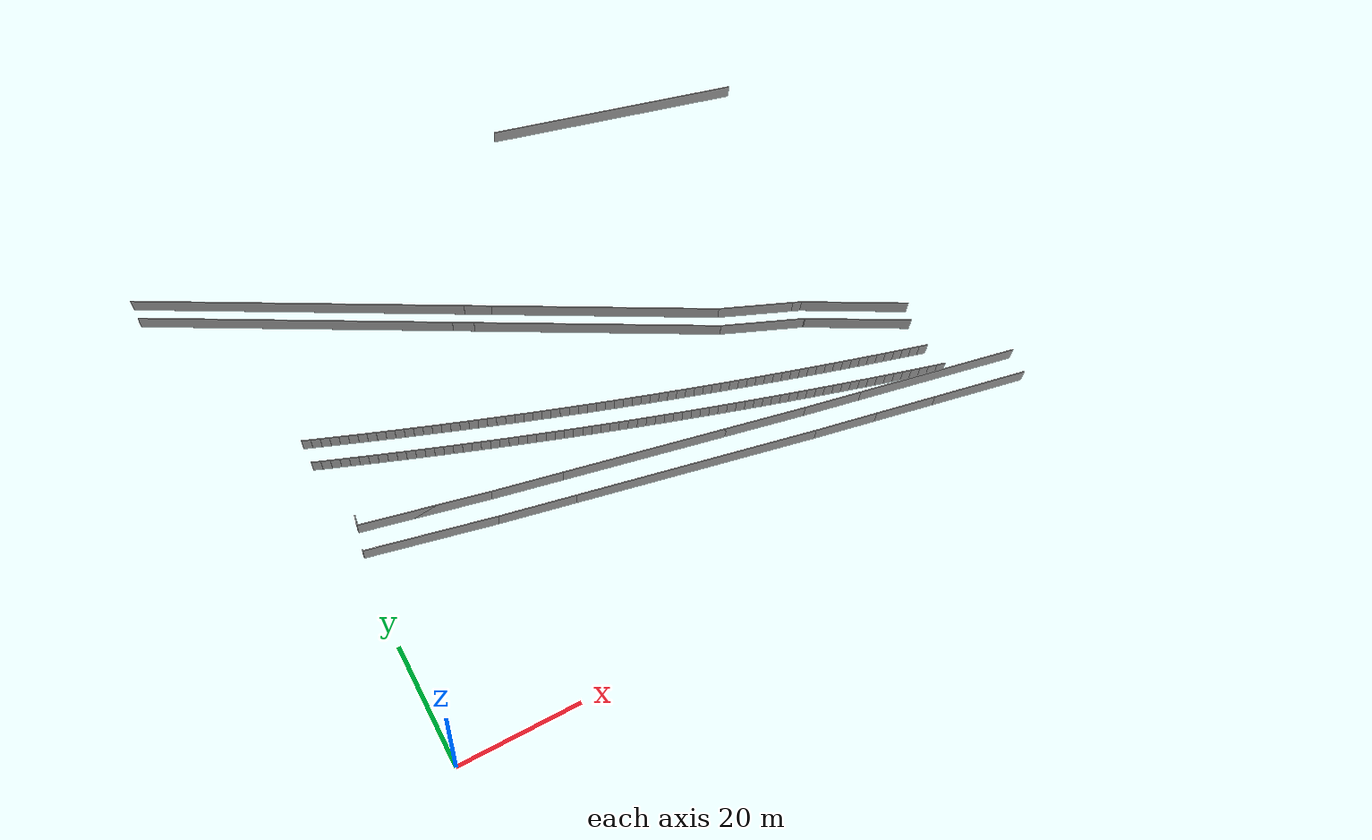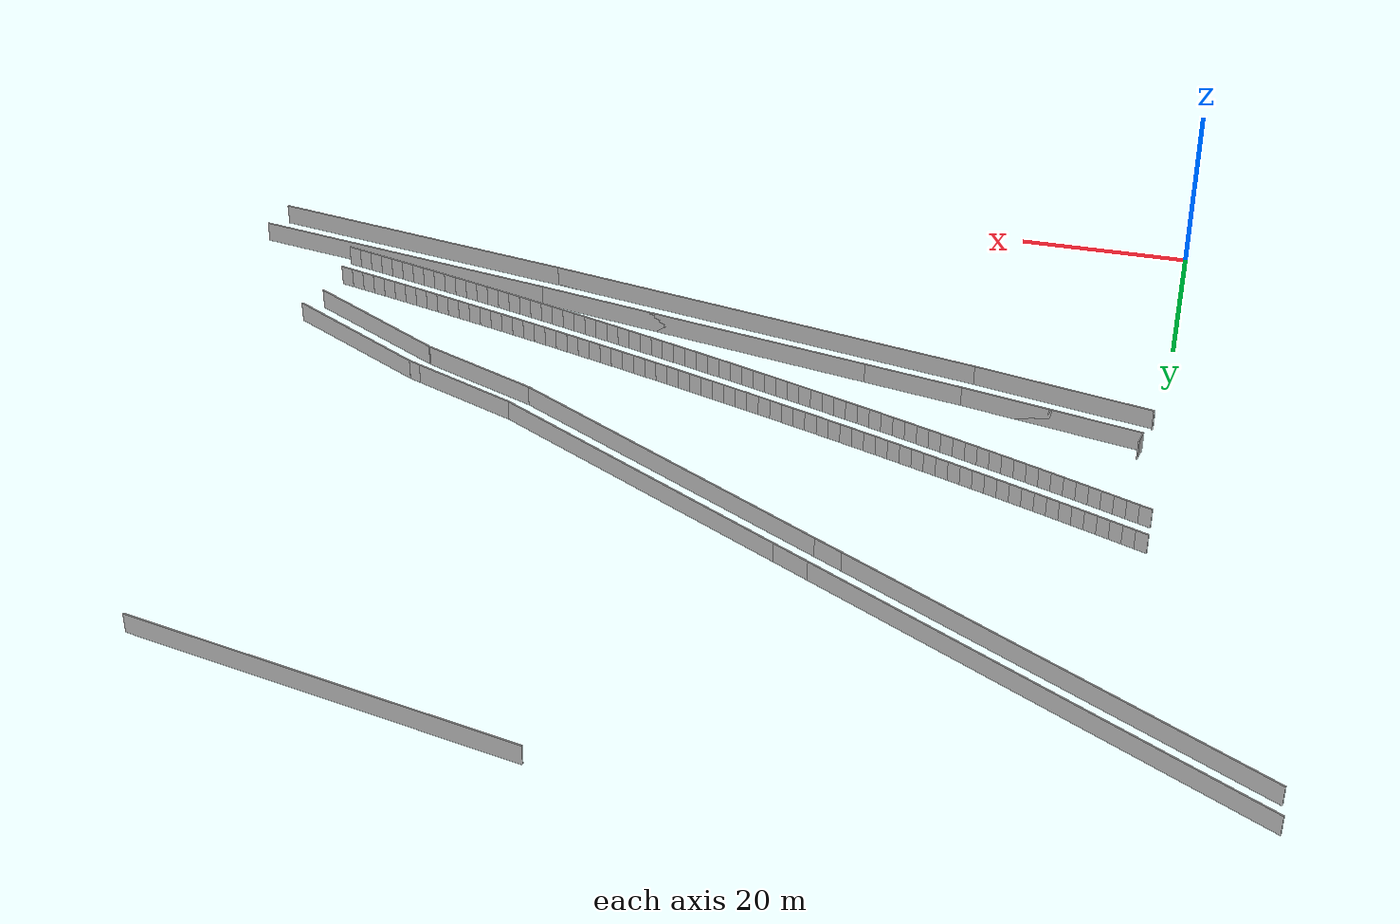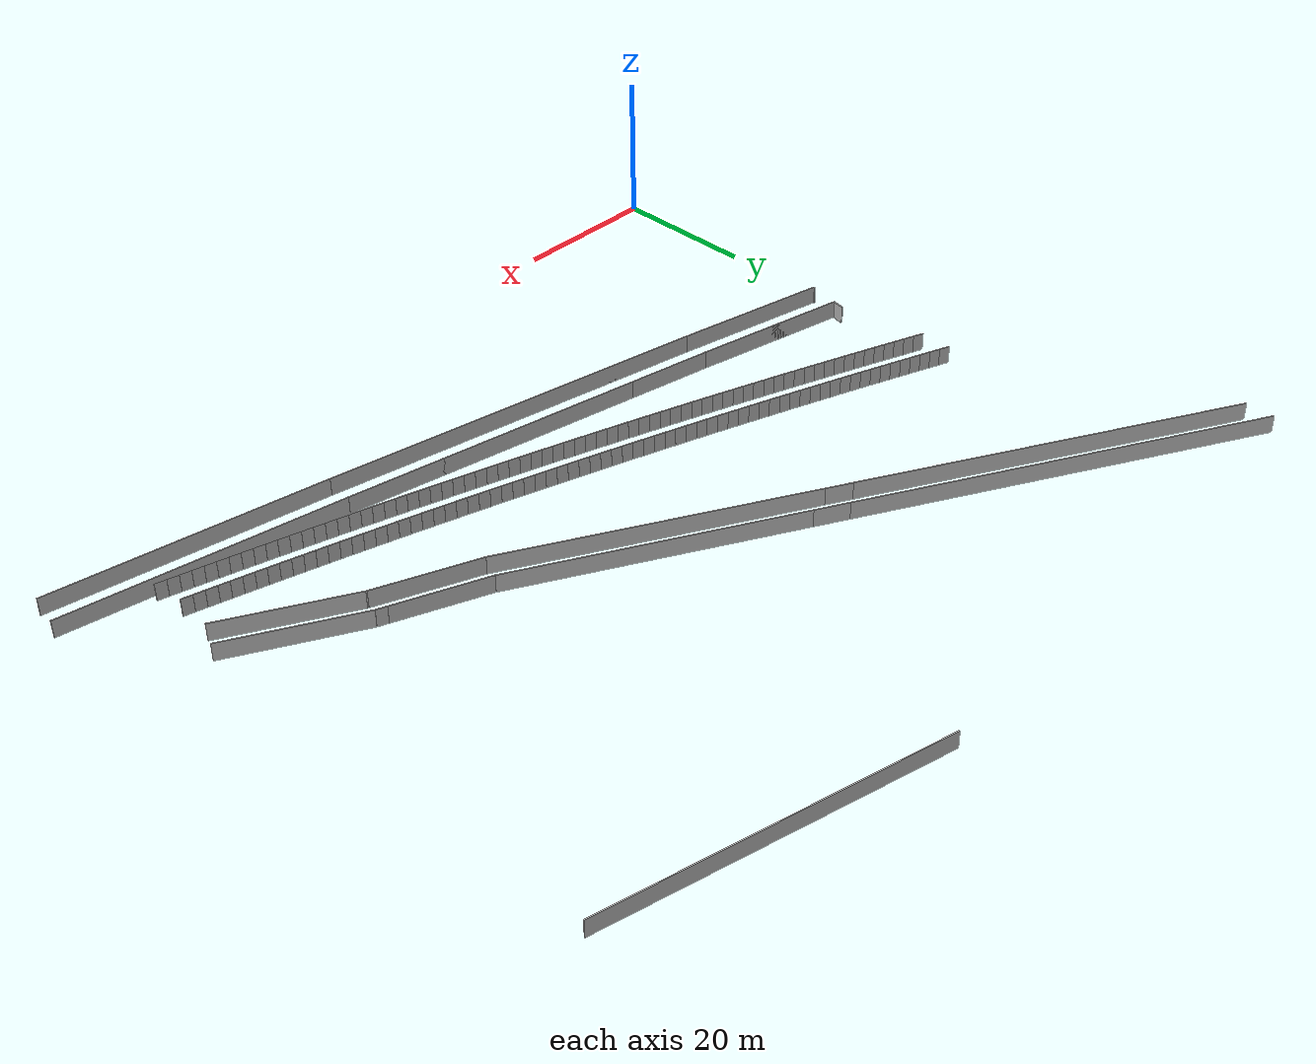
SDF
<?xml version="1.0" ?>
<sdf version="1.6">
  <model name="sps_0802">
    <pose frame="">0 0 0 0 -0 0</pose>
    <static>1</static>
    <self_collide>0</self_collide>
    <allow_auto_disable>0</allow_auto_disable>
    <link name="Wall27">
      <kinematic>0</kinematic>
      <gravity>1</gravity>
      <self_collide>0</self_collide>
      <collision name="collision">
        <geometry>
          <box>
            <size>21.2884 0.15 2.5</size>
          </box>
        </geometry>
        <pose frame="">0 0 0 0 -0 0</pose>
      </collision>
      <visual name="visual">
        <geometry>
          <box>
            <size>21.2884 0.15 2.5</size>
          </box>
        </geometry>
        <pose frame="">0 0 0 0 -0 0</pose>
        <cast_shadows>1</cast_shadows>
        <transparency>0.0</transparency>
      </visual>
      <pose frame="">11.6385 33.6256 1.25 0 -0 2.93723</pose>
    </link>
    <link name="Wall115">
      <kinematic>0</kinematic>
      <gravity>1</gravity>
      <self_collide>0</self_collide>
      <collision name="collision">
        <geometry>
          <box>
            <size>18.2188 0.15 2.5</size>
          </box>
        </geometry>
        <pose frame="">0 0 0 0 -0 0</pose>
      </collision>
      <visual name="visual">
        <geometry>
          <box>
            <size>18.2188 0.15 2.5</size>
          </box>
        </geometry>
        <pose frame="">0 0 0 0 -0 0</pose>
        <cast_shadows>1</cast_shadows>
        <transparency>0.0</transparency>
      </visual>
      <pose frame="">93.8209 39.7331 1.25 0 0 -0.498938</pose>
    </link>
    <link name="Wall116">
      <kinematic>0</kinematic>
      <gravity>1</gravity>
      <self_collide>0</self_collide>
      <collision name="collision">
        <geometry>
          <box>
            <size>10.5897 0.15 2.5</size>
          </box>
        </geometry>
        <pose frame="">0 0 0 0 -0 0</pose>
      </collision>
      <visual name="visual">
        <geometry>
          <box>
            <size>10.5897 0.15 2.5</size>
          </box>
        </geometry>
        <pose frame="">0 0 0 0 -0 0</pose>
        <cast_shadows>1</cast_shadows>
        <transparency>0.0</transparency>
      </visual>
      <pose frame="">79.2566 20.6364 1.25 0 0 -0.176184</pose>
    </link>
    <link name="Wall117">
      <kinematic>0</kinematic>
      <gravity>1</gravity>
      <self_collide>0</self_collide>
      <collision name="collision">
        <geometry>
          <box>
            <size>10.3568 0.15 2.5</size>
          </box>
        </geometry>
        <pose frame="">0 0 0 0 -0 0</pose>
      </collision>
      <visual name="visual">
        <geometry>
          <box>
            <size>10.3568 0.15 2.5</size>
          </box>
        </geometry>
        <pose frame="">0 0 0 0 -0 0</pose>
        <cast_shadows>1</cast_shadows>
        <transparency>0.0</transparency>
      </visual>
      <pose frame="">89.5677 18.8007 1.25 0 0 -0.176184</pose>
    </link>
    <link name="Wall189">
      <kinematic>0</kinematic>
      <gravity>1</gravity>
      <self_collide>0</self_collide>
      <collision name="collision">
        <geometry>
          <box>
            <size>41.7006 0.15 2.5</size>
          </box>
        </geometry>
        <pose frame="">0 0 0 0 -0 0</pose>
      </collision>
      <visual name="visual">
        <geometry>
          <box>
            <size>41.7006 0.15 2.5</size>
          </box>
        </geometry>
        <pose frame="">0 0 0 0 -0 0</pose>
        <cast_shadows>1</cast_shadows>
        <transparency>0.0</transparency>
      </visual>
      <pose frame="">52.7782 56.1772 1.25 0 -0 2.64268</pose>
    </link>
    <link name="Wall190">
      <kinematic>0</kinematic>
      <gravity>1</gravity>
      <self_collide>0</self_collide>
      <collision name="collision">
        <geometry>
          <box>
            <size>3.63576 0.15 2.5</size>
          </box>
        </geometry>
        <pose frame="">0 0 0 0 -0 0</pose>
      </collision>
      <visual name="visual">
        <geometry>
          <box>
            <size>3.63576 0.15 2.5</size>
          </box>
        </geometry>
        <pose frame="">0 0 0 0 -0 0</pose>
        <cast_shadows>1</cast_shadows>
        <transparency>0.0</transparency>
      </visual>
      <pose frame="">32.8732 67.0233 1.25 0 -0 2.64268</pose>
    </link>
    <link name="Wall191">
      <kinematic>0</kinematic>
      <gravity>1</gravity>
      <self_collide>0</self_collide>
      <collision name="collision">
        <geometry>
          <box>
            <size>53.3052 0.15 2.5</size>
          </box>
        </geometry>
        <pose frame="">0 0 0 0 -0 0</pose>
      </collision>
      <visual name="visual">
        <geometry>
          <box>
            <size>53.3052 0.15 2.5</size>
          </box>
        </geometry>
        <pose frame="">0 0 0 0 -0 0</pose>
        <cast_shadows>1</cast_shadows>
        <transparency>0.0</transparency>
      </visual>
      <pose frame="">7.87316 80.6456 1.25 0 -0 2.64268</pose>
    </link>
    <link name="Wall195">
      <kinematic>0</kinematic>
      <gravity>1</gravity>
      <self_collide>0</self_collide>
      <collision name="collision">
        <geometry>
          <box>
            <size>14.2591 0.15 2.5</size>
          </box>
        </geometry>
        <pose frame="">0 0 0 0 -0 0</pose>
      </collision>
      <visual name="visual">
        <geometry>
          <box>
            <size>14.2591 0.15 2.5</size>
          </box>
        </geometry>
        <pose frame="">0 0 0 0 -0 0</pose>
        <cast_shadows>1</cast_shadows>
        <transparency>0.0</transparency>
      </visual>
      <pose frame="">77.7093 43.5599 1.25 0 -0 2.76212</pose>
    </link>
    <link name="Wall282">
      <kinematic>0</kinematic>
      <gravity>1</gravity>
      <self_collide>0</self_collide>
      <collision name="collision">
        <geometry>
          <box>
            <size>1.74962 0.15 2.5</size>
          </box>
        </geometry>
        <pose frame="">0 0 0 0 -0 0</pose>
      </collision>
      <visual name="visual">
        <geometry>
          <box>
            <size>1.74962 0.15 2.5</size>
          </box>
        </geometry>
        <pose frame="">0 0 0 0 -0 0</pose>
        <cast_shadows>1</cast_shadows>
        <transparency>0.0</transparency>
      </visual>
      <pose frame="">2.29986 41.0501 1.25 0 -0 1.36638</pose>
    </link>
    <link name="Wall283">
      <kinematic>0</kinematic>
      <gravity>1</gravity>
      <self_collide>0</self_collide>
      <collision name="collision">
        <geometry>
          <box>
            <size>41.0751 0.15 2.5</size>
          </box>
        </geometry>
        <pose frame="">0 0 0 0 -0 0</pose>
      </collision>
      <visual name="visual">
        <geometry>
          <box>
            <size>41.0751 0.15 2.5</size>
          </box>
        </geometry>
        <pose frame="">0 0 0 0 -0 0</pose>
        <cast_shadows>1</cast_shadows>
        <transparency>0.0</transparency>
      </visual>
      <pose frame="">54.6443 29.8393 1.25 0 -0 2.95339</pose>
    </link>
    <link name="Wall284">
      <kinematic>0</kinematic>
      <gravity>1</gravity>
      <self_collide>0</self_collide>
      <collision name="collision">
        <geometry>
          <box>
            <size>11.7016 0.15 2.5</size>
          </box>
        </geometry>
        <pose frame="">0 0 0 0 -0 0</pose>
      </collision>
      <visual name="visual">
        <geometry>
          <box>
            <size>11.7016 0.15 2.5</size>
          </box>
        </geometry>
        <pose frame="">0 0 0 0 -0 0</pose>
        <cast_shadows>1</cast_shadows>
        <transparency>0.0</transparency>
      </visual>
      <pose frame="">28.7219 34.7762 1.25 0 -0 2.95339</pose>
    </link>
    <link name="Wall285">
      <kinematic>0</kinematic>
      <gravity>1</gravity>
      <self_collide>0</self_collide>
      <collision name="collision">
        <geometry>
          <box>
            <size>9.80231 0.15 2.5</size>
          </box>
        </geometry>
        <pose frame="">0 0 0 0 -0 0</pose>
      </collision>
      <visual name="visual">
        <geometry>
          <box>
            <size>9.80231 0.15 2.5</size>
          </box>
        </geometry>
        <pose frame="">0 0 0 0 -0 0</pose>
        <cast_shadows>1</cast_shadows>
        <transparency>0.0</transparency>
      </visual>
      <pose frame="">79.6443 25.1368 1.25 0 0 -0.176394</pose>
    </link>
    <link name="Wall286">
      <kinematic>0</kinematic>
      <gravity>1</gravity>
      <self_collide>0</self_collide>
      <collision name="collision">
        <geometry>
          <box>
            <size>27.6822 0.15 2.5</size>
          </box>
        </geometry>
        <pose frame="">0 0 0 0 -0 0</pose>
      </collision>
      <visual name="visual">
        <geometry>
          <box>
            <size>27.6822 0.15 2.5</size>
          </box>
        </geometry>
        <pose frame="">0 0 0 0 -0 0</pose>
        <cast_shadows>1</cast_shadows>
        <transparency>0.0</transparency>
      </visual>
      <pose frame="">98.0958 21.8479 1.25 0 0 -0.176394</pose>
    </link>
    <link name="Wall352">
      <kinematic>0</kinematic>
      <gravity>1</gravity>
      <self_collide>0</self_collide>
      <collision name="collision">
        <geometry>
          <box>
            <size>40.2857 0.15 2.5</size>
          </box>
        </geometry>
        <pose frame="">0 0 0 0 -0 0</pose>
      </collision>
      <visual name="visual">
        <geometry>
          <box>
            <size>40.2857 0.15 2.5</size>
          </box>
        </geometry>
        <pose frame="">0 0 0 0 -0 0</pose>
        <cast_shadows>1</cast_shadows>
        <transparency>0.0</transparency>
      </visual>
      <pose frame="">54.2566 25.3333 1.25 0 -0 2.95338</pose>
    </link>
    <link name="Wall353">
      <kinematic>0</kinematic>
      <gravity>1</gravity>
      <self_collide>0</self_collide>
      <collision name="collision">
        <geometry>
          <box>
            <size>12.6313 0.15 2.5</size>
          </box>
        </geometry>
        <pose frame="">0 0 0 0 -0 0</pose>
      </collision>
      <visual name="visual">
        <geometry>
          <box>
            <size>12.6313 0.15 2.5</size>
          </box>
        </geometry>
        <pose frame="">0 0 0 0 -0 0</pose>
        <cast_shadows>1</cast_shadows>
        <transparency>0.0</transparency>
      </visual>
      <pose frame="">28.2653 30.2838 1.25 0 -0 2.95338</pose>
    </link>
    <link name="Wall432">
      <kinematic>0</kinematic>
      <gravity>1</gravity>
      <self_collide>0</self_collide>
      <collision name="collision">
        <geometry>
          <box>
            <size>0.249531 0.15 2.5</size>
          </box>
        </geometry>
        <pose frame="">0 0 0 0 -0 0</pose>
      </collision>
      <visual name="visual">
        <geometry>
          <box>
            <size>0.249531 0.15 2.5</size>
          </box>
        </geometry>
        <pose frame="">0 0 0 0 -0 0</pose>
        <cast_shadows>1</cast_shadows>
        <transparency>0.0</transparency>
      </visual>
      <pose frame="">1.24105 35.9079 1.25 0 -0 1.36736</pose>
    </link>
    <link name="Wall433">
      <kinematic>0</kinematic>
      <gravity>1</gravity>
      <self_collide>0</self_collide>
      <collision name="collision">
        <geometry>
          <box>
            <size>12.8028 0.15 2.5</size>
          </box>
        </geometry>
        <pose frame="">0 0 0 0 -0 0</pose>
      </collision>
      <visual name="visual">
        <geometry>
          <box>
            <size>12.8028 0.15 2.5</size>
          </box>
        </geometry>
        <pose frame="">0 0 0 0 -0 0</pose>
        <cast_shadows>1</cast_shadows>
        <transparency>0.0</transparency>
      </visual>
      <pose frame="">78.5235 47.0026 1.25 0 0 -0.379479</pose>
    </link>
    <link name="Wall434">
      <kinematic>0</kinematic>
      <gravity>1</gravity>
      <self_collide>0</self_collide>
      <collision name="collision">
        <geometry>
          <box>
            <size>1.4562 0.15 2.5</size>
          </box>
        </geometry>
        <pose frame="">0 0 0 0 -0 0</pose>
      </collision>
      <visual name="visual">
        <geometry>
          <box>
            <size>1.4562 0.15 2.5</size>
          </box>
        </geometry>
        <pose frame="">0 0 0 0 -0 0</pose>
        <cast_shadows>1</cast_shadows>
        <transparency>0.0</transparency>
      </visual>
      <pose frame="">85.1457 44.3616 1.25 0 0 -0.379479</pose>
    </link>
    <link name="Wall529">
      <kinematic>0</kinematic>
      <gravity>1</gravity>
      <self_collide>0</self_collide>
      <collision name="collision">
        <geometry>
          <box>
            <size>56.9411 0.15 2.5</size>
          </box>
        </geometry>
        <pose frame="">0 0 0 0 -0 0</pose>
      </collision>
      <visual name="visual">
        <geometry>
          <box>
            <size>56.9411 0.15 2.5</size>
          </box>
        </geometry>
        <pose frame="">0 0 0 0 -0 0</pose>
        <cast_shadows>1</cast_shadows>
        <transparency>0.0</transparency>
      </visual>
      <pose frame="">9.46944 83.7614 1.25 0 0 -0.498918</pose>
    </link>
    <link name="Wall530">
      <kinematic>0</kinematic>
      <gravity>1</gravity>
      <self_collide>0</self_collide>
      <collision name="collision">
        <geometry>
          <box>
            <size>4.69376 0.15 2.5</size>
          </box>
        </geometry>
        <pose frame="">0 0 0 0 -0 0</pose>
      </collision>
      <visual name="visual">
        <geometry>
          <box>
            <size>4.69376 0.15 2.5</size>
          </box>
        </geometry>
        <pose frame="">0 0 0 0 -0 0</pose>
        <cast_shadows>1</cast_shadows>
        <transparency>0.0</transparency>
      </visual>
      <pose frame="">36.5302 69.016 1.25 0 0 -0.498918</pose>
    </link>
    <link name="Wall531">
      <kinematic>0</kinematic>
      <gravity>1</gravity>
      <self_collide>0</self_collide>
      <collision name="collision">
        <geometry>
          <box>
            <size>38.7045 0.15 2.5</size>
          </box>
        </geometry>
        <pose frame="">0 0 0 0 -0 0</pose>
      </collision>
      <visual name="visual">
        <geometry>
          <box>
            <size>38.7045 0.15 2.5</size>
          </box>
        </geometry>
        <pose frame="">0 0 0 0 -0 0</pose>
        <cast_shadows>1</cast_shadows>
        <transparency>0.0</transparency>
      </visual>
      <pose frame="">55.5843 58.6335 1.25 0 0 -0.498918</pose>
    </link>
    <link name="Wall611">
      <kinematic>0</kinematic>
      <gravity>1</gravity>
      <self_collide>0</self_collide>
      <collision name="collision">
        <geometry>
          <box>
            <size>21.2955 0.15 2.5</size>
          </box>
        </geometry>
        <pose frame="">0 0 0 0 -0 0</pose>
      </collision>
      <visual name="visual">
        <geometry>
          <box>
            <size>21.2955 0.15 2.5</size>
          </box>
        </geometry>
        <pose frame="">0 0 0 0 -0 0</pose>
        <cast_shadows>1</cast_shadows>
        <transparency>0.0</transparency>
      </visual>
      <pose frame="">12.5484 38.0322 1.25 0 -0 2.93719</pose>
    </link>
    <link name="Wall612">
      <kinematic>0</kinematic>
      <gravity>1</gravity>
      <self_collide>0</self_collide>
      <collision name="collision">
        <geometry>
          <box>
            <size>17.9531 0.15 2.5</size>
          </box>
        </geometry>
        <pose frame="">0 0 0 0 -0 0</pose>
      </collision>
      <visual name="visual">
        <geometry>
          <box>
            <size>17.9531 0.15 2.5</size>
          </box>
        </geometry>
        <pose frame="">0 0 0 0 -0 0</pose>
        <cast_shadows>1</cast_shadows>
        <transparency>0.0</transparency>
      </visual>
      <pose frame="">92.3516 36.5486 1.25 0 -0 2.64265</pose>
    </link>
    <link name="Wall613">
      <kinematic>0</kinematic>
      <gravity>1</gravity>
      <self_collide>0</self_collide>
      <collision name="collision">
        <geometry>
          <box>
            <size>0.156951 0.15 2.5</size>
          </box>
        </geometry>
        <pose frame="">0 0 0 0 -0 0</pose>
      </collision>
      <visual name="visual">
        <geometry>
          <box>
            <size>0.156951 0.15 2.5</size>
          </box>
        </geometry>
        <pose frame="">0 0 0 0 -0 0</pose>
        <cast_shadows>1</cast_shadows>
        <transparency>0.0</transparency>
      </visual>
      <pose frame="">84.4005 40.8813 1.25 0 -0 2.64265</pose>
    </link>
    <link name="Wall996">
      <kinematic>0</kinematic>
      <gravity>1</gravity>
      <self_collide>0</self_collide>
      <collision name="collision">
        <geometry>
          <box>
            <size>37.2045 0.15 2.5</size>
          </box>
        </geometry>
        <pose frame="">0 0 0 0 -0 0</pose>
      </collision>
      <visual name="visual">
        <geometry>
          <box>
            <size>37.2045 0.15 2.5</size>
          </box>
        </geometry>
        <pose frame="">0 0 0 0 -0 0</pose>
        <cast_shadows>1</cast_shadows>
        <transparency>0.0</transparency>
      </visual>
      <pose frame="">92.358 18.304 1.25 0 -0 2.96541</pose>
    </link>
    <link name="Wall997">
      <kinematic>0</kinematic>
      <gravity>1</gravity>
      <self_collide>0</self_collide>
      <collision name="collision">
        <geometry>
          <box>
            <size>52.9169 0.15 2.5</size>
          </box>
        </geometry>
        <pose frame="">0 0 0 0 -0 0</pose>
      </collision>
      <visual name="visual">
        <geometry>
          <box>
            <size>52.9169 0.15 2.5</size>
          </box>
        </geometry>
        <pose frame="">0 0 0 0 -0 0</pose>
        <cast_shadows>1</cast_shadows>
        <transparency>0.0</transparency>
      </visual>
      <pose frame="">48.0525 26.515 1.25 0 -0 2.95338</pose>
    </link>
    <link name="Wall998">
      <kinematic>0</kinematic>
      <gravity>1</gravity>
      <self_collide>0</self_collide>
      <collision name="collision">
        <geometry>
          <box>
            <size>21.2884 0.15 2.5</size>
          </box>
        </geometry>
        <pose frame="">0 0 0 0 -0 0</pose>
      </collision>
      <visual name="visual">
        <geometry>
          <box>
            <size>21.2884 0.15 2.5</size>
          </box>
        </geometry>
        <pose frame="">0 0 0 0 -0 0</pose>
        <cast_shadows>1</cast_shadows>
        <transparency>0.0</transparency>
      </visual>
      <pose frame="">11.6385 33.6256 1.25 0 -0 2.93723</pose>
    </link>
    <link name="Wall999">
      <kinematic>0</kinematic>
      <gravity>1</gravity>
      <self_collide>0</self_collide>
      <collision name="collision">
        <geometry>
          <box>
            <size>0.249531 0.15 2.5</size>
          </box>
        </geometry>
        <pose frame="">0 0 0 0 -0 0</pose>
      </collision>
      <visual name="visual">
        <geometry>
          <box>
            <size>0.249531 0.15 2.5</size>
          </box>
        </geometry>
        <pose frame="">0 0 0 0 -0 0</pose>
        <cast_shadows>1</cast_shadows>
        <transparency>0.0</transparency>
      </visual>
      <pose frame="">1.24105 35.9079 1.25 0 -0 1.36736</pose>
    </link>
    <link name="Wall1003">
      <kinematic>0</kinematic>
      <gravity>1</gravity>
      <self_collide>0</self_collide>
      <collision name="collision">
        <geometry>
          <box>
            <size>1.74962 0.15 2.5</size>
          </box>
        </geometry>
        <pose frame="">0 0 0 0 -0 0</pose>
      </collision>
      <visual name="visual">
        <geometry>
          <box>
            <size>1.74962 0.15 2.5</size>
          </box>
        </geometry>
        <pose frame="">0 0 0 0 -0 0</pose>
        <cast_shadows>1</cast_shadows>
        <transparency>0.0</transparency>
      </visual>
      <pose frame="">2.29986 41.0501 1.25 0 0 -1.77521</pose>
    </link>
    <link name="Wall1004">
      <kinematic>0</kinematic>
      <gravity>1</gravity>
      <self_collide>0</self_collide>
      <collision name="collision">
        <geometry>
          <box>
            <size>21.2955 0.15 2.5</size>
          </box>
        </geometry>
        <pose frame="">0 0 0 0 -0 0</pose>
      </collision>
      <visual name="visual">
        <geometry>
          <box>
            <size>21.2955 0.15 2.5</size>
          </box>
        </geometry>
        <pose frame="">0 0 0 0 -0 0</pose>
        <cast_shadows>1</cast_shadows>
        <transparency>0.0</transparency>
      </visual>
      <pose frame="">12.5484 38.0322 1.25 0 0 -0.204404</pose>
    </link>
    <link name="Wall1005">
      <kinematic>0</kinematic>
      <gravity>1</gravity>
      <self_collide>0</self_collide>
      <collision name="collision">
        <geometry>
          <box>
            <size>52.7767 0.15 2.5</size>
          </box>
        </geometry>
        <pose frame="">0 0 0 0 -0 0</pose>
      </collision>
      <visual name="visual">
        <geometry>
          <box>
            <size>52.7767 0.15 2.5</size>
          </box>
        </geometry>
        <pose frame="">0 0 0 0 -0 0</pose>
        <cast_shadows>1</cast_shadows>
        <transparency>0.0</transparency>
      </visual>
      <pose frame="">48.8968 30.9339 1.25 0 0 -0.188199</pose>
    </link>
    <link name="Wall1006">
      <kinematic>0</kinematic>
      <gravity>1</gravity>
      <self_collide>0</self_collide>
      <collision name="collision">
        <geometry>
          <box>
            <size>37.4845 0.15 2.5</size>
          </box>
        </geometry>
        <pose frame="">0 0 0 0 -0 0</pose>
      </collision>
      <visual name="visual">
        <geometry>
          <box>
            <size>37.4845 0.15 2.5</size>
          </box>
        </geometry>
        <pose frame="">0 0 0 0 -0 0</pose>
        <cast_shadows>1</cast_shadows>
        <transparency>0.0</transparency>
      </visual>
      <pose frame="">93.2707 22.708 1.25 0 0 -0.176394</pose>
    </link>
    <link name="Wall6628">
      <kinematic>0</kinematic>
      <gravity>1</gravity>
      <self_collide>0</self_collide>
      <collision name="collision">
        <geometry>
          <box>
            <size>45.9415 0.15 2.5</size>
          </box>
        </geometry>
        <pose frame="">0 0 0 0 -0 0</pose>
      </collision>
      <visual name="visual">
        <geometry>
          <box>
            <size>45.9415 0.15 2.5</size>
          </box>
        </geometry>
        <pose frame="">0 0 0 0 -0 0</pose>
        <cast_shadows>1</cast_shadows>
        <transparency>0.0</transparency>
      </visual>
      <pose frame="">78.7053 98.127 1.25 0 -0 2.9176</pose>
    </link>
    <link name="Wall8823">
      <kinematic>0</kinematic>
      <gravity>1</gravity>
      <self_collide>0</self_collide>
      <collision name="collision">
        <geometry>
          <box>
            <size>1.49888 0.15 2.5</size>
          </box>
        </geometry>
        <pose frame="">0 0 0 0 -0 0</pose>
      </collision>
      <visual name="visual">
        <geometry>
          <box>
            <size>1.49888 0.15 2.5</size>
          </box>
        </geometry>
        <pose frame="">0 0 0 0 -0 0</pose>
        <cast_shadows>1</cast_shadows>
        <transparency>0.0</transparency>
      </visual>
      <pose frame="">0.735038 53.5175 1.25 0 0 -0.357736</pose>
    </link>
    <link name="Wall8824">
      <kinematic>0</kinematic>
      <gravity>1</gravity>
      <self_collide>0</self_collide>
      <collision name="collision">
        <geometry>
          <box>
            <size>1.49896 0.15 2.5</size>
          </box>
        </geometry>
        <pose frame="">0 0 0 0 -0 0</pose>
      </collision>
      <visual name="visual">
        <geometry>
          <box>
            <size>1.49896 0.15 2.5</size>
          </box>
        </geometry>
        <pose frame="">0 0 0 0 -0 0</pose>
        <cast_shadows>1</cast_shadows>
        <transparency>0.0</transparency>
      </visual>
      <pose frame="">2.13946 52.9937 1.25 0 0 -0.35624</pose>
    </link>
    <link name="Wall8825">
      <kinematic>0</kinematic>
      <gravity>1</gravity>
      <self_collide>0</self_collide>
      <collision name="collision">
        <geometry>
          <box>
            <size>1.49893 0.15 2.5</size>
          </box>
        </geometry>
        <pose frame="">0 0 0 0 -0 0</pose>
      </collision>
      <visual name="visual">
        <geometry>
          <box>
            <size>1.49893 0.15 2.5</size>
          </box>
        </geometry>
        <pose frame="">0 0 0 0 -0 0</pose>
        <cast_shadows>1</cast_shadows>
        <transparency>0.0</transparency>
      </visual>
      <pose frame="">3.54476 52.4722 1.25 0 0 -0.354424</pose>
    </link>
    <link name="Wall8826">
      <kinematic>0</kinematic>
      <gravity>1</gravity>
      <self_collide>0</self_collide>
      <collision name="collision">
        <geometry>
          <box>
            <size>1.49911 0.15 2.5</size>
          </box>
        </geometry>
        <pose frame="">0 0 0 0 -0 0</pose>
      </collision>
      <visual name="visual">
        <geometry>
          <box>
            <size>1.49911 0.15 2.5</size>
          </box>
        </geometry>
        <pose frame="">0 0 0 0 -0 0</pose>
        <cast_shadows>1</cast_shadows>
        <transparency>0.0</transparency>
      </visual>
      <pose frame="">4.95095 51.9529 1.25 0 0 -0.353119</pose>
    </link>
    <link name="Wall8827">
      <kinematic>0</kinematic>
      <gravity>1</gravity>
      <self_collide>0</self_collide>
      <collision name="collision">
        <geometry>
          <box>
            <size>1.49878 0.15 2.5</size>
          </box>
        </geometry>
        <pose frame="">0 0 0 0 -0 0</pose>
      </collision>
      <visual name="visual">
        <geometry>
          <box>
            <size>1.49878 0.15 2.5</size>
          </box>
        </geometry>
        <pose frame="">0 0 0 0 -0 0</pose>
        <cast_shadows>1</cast_shadows>
        <transparency>0.0</transparency>
      </visual>
      <pose frame="">6.35787 51.4358 1.25 0 0 -0.351335</pose>
    </link>
    <link name="Wall8828">
      <kinematic>0</kinematic>
      <gravity>1</gravity>
      <self_collide>0</self_collide>
      <collision name="collision">
        <geometry>
          <box>
            <size>1.49895 0.15 2.5</size>
          </box>
        </geometry>
        <pose frame="">0 0 0 0 -0 0</pose>
      </collision>
      <visual name="visual">
        <geometry>
          <box>
            <size>1.49895 0.15 2.5</size>
          </box>
        </geometry>
        <pose frame="">0 0 0 0 -0 0</pose>
        <cast_shadows>1</cast_shadows>
        <transparency>0.0</transparency>
      </visual>
      <pose frame="">7.76556 50.921 1.25 0 0 -0.349863</pose>
    </link>
    <link name="Wall8829">
      <kinematic>0</kinematic>
      <gravity>1</gravity>
      <self_collide>0</self_collide>
      <collision name="collision">
        <geometry>
          <box>
            <size>1.49883 0.15 2.5</size>
          </box>
        </geometry>
        <pose frame="">0 0 0 0 -0 0</pose>
      </collision>
      <visual name="visual">
        <geometry>
          <box>
            <size>1.49883 0.15 2.5</size>
          </box>
        </geometry>
        <pose frame="">0 0 0 0 -0 0</pose>
        <cast_shadows>1</cast_shadows>
        <transparency>0.0</transparency>
      </visual>
      <pose frame="">9.17403 50.4083 1.25 0 0 -0.348333</pose>
    </link>
    <link name="Wall8830">
      <kinematic>0</kinematic>
      <gravity>1</gravity>
      <self_collide>0</self_collide>
      <collision name="collision">
        <geometry>
          <box>
            <size>1.499 0.15 2.5</size>
          </box>
        </geometry>
        <pose frame="">0 0 0 0 -0 0</pose>
      </collision>
      <visual name="visual">
        <geometry>
          <box>
            <size>1.499 0.15 2.5</size>
          </box>
        </geometry>
        <pose frame="">0 0 0 0 -0 0</pose>
        <cast_shadows>1</cast_shadows>
        <transparency>0.0</transparency>
      </visual>
      <pose frame="">10.5833 49.8978 1.25 0 0 -0.346732</pose>
    </link>
    <link name="Wall8831">
      <kinematic>0</kinematic>
      <gravity>1</gravity>
      <self_collide>0</self_collide>
      <collision name="collision">
        <geometry>
          <box>
            <size>1.49897 0.15 2.5</size>
          </box>
        </geometry>
        <pose frame="">0 0 0 0 -0 0</pose>
      </collision>
      <visual name="visual">
        <geometry>
          <box>
            <size>1.49897 0.15 2.5</size>
          </box>
        </geometry>
        <pose frame="">0 0 0 0 -0 0</pose>
        <cast_shadows>1</cast_shadows>
        <transparency>0.0</transparency>
      </visual>
      <pose frame="">11.9936 49.3896 1.25 0 0 -0.345007</pose>
    </link>
    <link name="Wall8832">
      <kinematic>0</kinematic>
      <gravity>1</gravity>
      <self_collide>0</self_collide>
      <collision name="collision">
        <geometry>
          <box>
            <size>1.499 0.15 2.5</size>
          </box>
        </geometry>
        <pose frame="">0 0 0 0 -0 0</pose>
      </collision>
      <visual name="visual">
        <geometry>
          <box>
            <size>1.499 0.15 2.5</size>
          </box>
        </geometry>
        <pose frame="">0 0 0 0 -0 0</pose>
        <cast_shadows>1</cast_shadows>
        <transparency>0.0</transparency>
      </visual>
      <pose frame="">13.4046 48.8836 1.25 0 0 -0.343616</pose>
    </link>
    <link name="Wall8833">
      <kinematic>0</kinematic>
      <gravity>1</gravity>
      <self_collide>0</self_collide>
      <collision name="collision">
        <geometry>
          <box>
            <size>1.49901 0.15 2.5</size>
          </box>
        </geometry>
        <pose frame="">0 0 0 0 -0 0</pose>
      </collision>
      <visual name="visual">
        <geometry>
          <box>
            <size>1.49901 0.15 2.5</size>
          </box>
        </geometry>
        <pose frame="">0 0 0 0 -0 0</pose>
        <cast_shadows>1</cast_shadows>
        <transparency>0.0</transparency>
      </visual>
      <pose frame="">14.8164 48.3798 1.25 0 0 -0.341928</pose>
    </link>
    <link name="Wall8834">
      <kinematic>0</kinematic>
      <gravity>1</gravity>
      <self_collide>0</self_collide>
      <collision name="collision">
        <geometry>
          <box>
            <size>1.49896 0.15 2.5</size>
          </box>
        </geometry>
        <pose frame="">0 0 0 0 -0 0</pose>
      </collision>
      <visual name="visual">
        <geometry>
          <box>
            <size>1.49896 0.15 2.5</size>
          </box>
        </geometry>
        <pose frame="">0 0 0 0 -0 0</pose>
        <cast_shadows>1</cast_shadows>
        <transparency>0.0</transparency>
      </visual>
      <pose frame="">16.229 47.8783 1.25 0 0 -0.340384</pose>
    </link>
    <link name="Wall8835">
      <kinematic>0</kinematic>
      <gravity>1</gravity>
      <self_collide>0</self_collide>
      <collision name="collision">
        <geometry>
          <box>
            <size>1.49902 0.15 2.5</size>
          </box>
        </geometry>
        <pose frame="">0 0 0 0 -0 0</pose>
      </collision>
      <visual name="visual">
        <geometry>
          <box>
            <size>1.49902 0.15 2.5</size>
          </box>
        </geometry>
        <pose frame="">0 0 0 0 -0 0</pose>
        <cast_shadows>1</cast_shadows>
        <transparency>0.0</transparency>
      </visual>
      <pose frame="">17.6424 47.379 1.25 0 0 -0.338773</pose>
    </link>
    <link name="Wall8836">
      <kinematic>0</kinematic>
      <gravity>1</gravity>
      <self_collide>0</self_collide>
      <collision name="collision">
        <geometry>
          <box>
            <size>1.49883 0.15 2.5</size>
          </box>
        </geometry>
        <pose frame="">0 0 0 0 -0 0</pose>
      </collision>
      <visual name="visual">
        <geometry>
          <box>
            <size>1.49883 0.15 2.5</size>
          </box>
        </geometry>
        <pose frame="">0 0 0 0 -0 0</pose>
        <cast_shadows>1</cast_shadows>
        <transparency>0.0</transparency>
      </visual>
      <pose frame="">19.0564 46.8819 1.25 0 0 -0.337307</pose>
    </link>
    <link name="Wall8837">
      <kinematic>0</kinematic>
      <gravity>1</gravity>
      <self_collide>0</self_collide>
      <collision name="collision">
        <geometry>
          <box>
            <size>1.49883 0.15 2.5</size>
          </box>
        </geometry>
        <pose frame="">0 0 0 0 -0 0</pose>
      </collision>
      <visual name="visual">
        <geometry>
          <box>
            <size>1.49883 0.15 2.5</size>
          </box>
        </geometry>
        <pose frame="">0 0 0 0 -0 0</pose>
        <cast_shadows>1</cast_shadows>
        <transparency>0.0</transparency>
      </visual>
      <pose frame="">20.4712 46.3871 1.25 0 0 -0.335581</pose>
    </link>
    <link name="Wall8838">
      <kinematic>0</kinematic>
      <gravity>1</gravity>
      <self_collide>0</self_collide>
      <collision name="collision">
        <geometry>
          <box>
            <size>1.49903 0.15 2.5</size>
          </box>
        </geometry>
        <pose frame="">0 0 0 0 -0 0</pose>
      </collision>
      <visual name="visual">
        <geometry>
          <box>
            <size>1.49903 0.15 2.5</size>
          </box>
        </geometry>
        <pose frame="">0 0 0 0 -0 0</pose>
        <cast_shadows>1</cast_shadows>
        <transparency>0.0</transparency>
      </visual>
      <pose frame="">21.887 45.8946 1.25 0 0 -0.333983</pose>
    </link>
    <link name="Wall8839">
      <kinematic>0</kinematic>
      <gravity>1</gravity>
      <self_collide>0</self_collide>
      <collision name="collision">
        <geometry>
          <box>
            <size>1.49889 0.15 2.5</size>
          </box>
        </geometry>
        <pose frame="">0 0 0 0 -0 0</pose>
      </collision>
      <visual name="visual">
        <geometry>
          <box>
            <size>1.49889 0.15 2.5</size>
          </box>
        </geometry>
        <pose frame="">0 0 0 0 -0 0</pose>
        <cast_shadows>1</cast_shadows>
        <transparency>0.0</transparency>
      </visual>
      <pose frame="">23.3035 45.4043 1.25 0 0 -0.332464</pose>
    </link>
    <link name="Wall8840">
      <kinematic>0</kinematic>
      <gravity>1</gravity>
      <self_collide>0</self_collide>
      <collision name="collision">
        <geometry>
          <box>
            <size>1.49909 0.15 2.5</size>
          </box>
        </geometry>
        <pose frame="">0 0 0 0 -0 0</pose>
      </collision>
      <visual name="visual">
        <geometry>
          <box>
            <size>1.49909 0.15 2.5</size>
          </box>
        </geometry>
        <pose frame="">0 0 0 0 -0 0</pose>
        <cast_shadows>1</cast_shadows>
        <transparency>0.0</transparency>
      </visual>
      <pose frame="">24.7208 44.9162 1.25 0 0 -0.330866</pose>
    </link>
    <link name="Wall8841">
      <kinematic>0</kinematic>
      <gravity>1</gravity>
      <self_collide>0</self_collide>
      <collision name="collision">
        <geometry>
          <box>
            <size>1.49896 0.15 2.5</size>
          </box>
        </geometry>
        <pose frame="">0 0 0 0 -0 0</pose>
      </collision>
      <visual name="visual">
        <geometry>
          <box>
            <size>1.49896 0.15 2.5</size>
          </box>
        </geometry>
        <pose frame="">0 0 0 0 -0 0</pose>
        <cast_shadows>1</cast_shadows>
        <transparency>0.0</transparency>
      </visual>
      <pose frame="">26.1388 44.4303 1.25 0 0 -0.329348</pose>
    </link>
    <link name="Wall8842">
      <kinematic>0</kinematic>
      <gravity>1</gravity>
      <self_collide>0</self_collide>
      <collision name="collision">
        <geometry>
          <box>
            <size>1.49883 0.15 2.5</size>
          </box>
        </geometry>
        <pose frame="">0 0 0 0 -0 0</pose>
      </collision>
      <visual name="visual">
        <geometry>
          <box>
            <size>1.49883 0.15 2.5</size>
          </box>
        </geometry>
        <pose frame="">0 0 0 0 -0 0</pose>
        <cast_shadows>1</cast_shadows>
        <transparency>0.0</transparency>
      </visual>
      <pose frame="">27.5575 43.9466 1.25 0 0 -0.327829</pose>
    </link>
    <link name="Wall8843">
      <kinematic>0</kinematic>
      <gravity>1</gravity>
      <self_collide>0</self_collide>
      <collision name="collision">
        <geometry>
          <box>
            <size>1.49897 0.15 2.5</size>
          </box>
        </geometry>
        <pose frame="">0 0 0 0 -0 0</pose>
      </collision>
      <visual name="visual">
        <geometry>
          <box>
            <size>1.49897 0.15 2.5</size>
          </box>
        </geometry>
        <pose frame="">0 0 0 0 -0 0</pose>
        <cast_shadows>1</cast_shadows>
        <transparency>0.0</transparency>
      </visual>
      <pose frame="">28.977 43.4652 1.25 0 0 -0.326077</pose>
    </link>
    <link name="Wall8844">
      <kinematic>0</kinematic>
      <gravity>1</gravity>
      <self_collide>0</self_collide>
      <collision name="collision">
        <geometry>
          <box>
            <size>1.49886 0.15 2.5</size>
          </box>
        </geometry>
        <pose frame="">0 0 0 0 -0 0</pose>
      </collision>
      <visual name="visual">
        <geometry>
          <box>
            <size>1.49886 0.15 2.5</size>
          </box>
        </geometry>
        <pose frame="">0 0 0 0 -0 0</pose>
        <cast_shadows>1</cast_shadows>
        <transparency>0.0</transparency>
      </visual>
      <pose frame="">30.3973 42.9861 1.25 0 0 -0.324596</pose>
    </link>
    <link name="Wall8845">
      <kinematic>0</kinematic>
      <gravity>1</gravity>
      <self_collide>0</self_collide>
      <collision name="collision">
        <geometry>
          <box>
            <size>1.49896 0.15 2.5</size>
          </box>
        </geometry>
        <pose frame="">0 0 0 0 -0 0</pose>
      </collision>
      <visual name="visual">
        <geometry>
          <box>
            <size>1.49896 0.15 2.5</size>
          </box>
        </geometry>
        <pose frame="">0 0 0 0 -0 0</pose>
        <cast_shadows>1</cast_shadows>
        <transparency>0.0</transparency>
      </visual>
      <pose frame="">31.8184 42.5092 1.25 0 0 -0.322987</pose>
    </link>
    <link name="Wall8846">
      <kinematic>0</kinematic>
      <gravity>1</gravity>
      <self_collide>0</self_collide>
      <collision name="collision">
        <geometry>
          <box>
            <size>1.49909 0.15 2.5</size>
          </box>
        </geometry>
        <pose frame="">0 0 0 0 -0 0</pose>
      </collision>
      <visual name="visual">
        <geometry>
          <box>
            <size>1.49909 0.15 2.5</size>
          </box>
        </geometry>
        <pose frame="">0 0 0 0 -0 0</pose>
        <cast_shadows>1</cast_shadows>
        <transparency>0.0</transparency>
      </visual>
      <pose frame="">33.2403 42.0346 1.25 0 0 -0.321326</pose>
    </link>
    <link name="Wall8847">
      <kinematic>0</kinematic>
      <gravity>1</gravity>
      <self_collide>0</self_collide>
      <collision name="collision">
        <geometry>
          <box>
            <size>1.49884 0.15 2.5</size>
          </box>
        </geometry>
        <pose frame="">0 0 0 0 -0 0</pose>
      </collision>
      <visual name="visual">
        <geometry>
          <box>
            <size>1.49884 0.15 2.5</size>
          </box>
        </geometry>
        <pose frame="">0 0 0 0 -0 0</pose>
        <cast_shadows>1</cast_shadows>
        <transparency>0.0</transparency>
      </visual>
      <pose frame="">34.6628 41.5622 1.25 0 0 -0.319922</pose>
    </link>
    <link name="Wall8848">
      <kinematic>0</kinematic>
      <gravity>1</gravity>
      <self_collide>0</self_collide>
      <collision name="collision">
        <geometry>
          <box>
            <size>1.49891 0.15 2.5</size>
          </box>
        </geometry>
        <pose frame="">0 0 0 0 -0 0</pose>
      </collision>
      <visual name="visual">
        <geometry>
          <box>
            <size>1.49891 0.15 2.5</size>
          </box>
        </geometry>
        <pose frame="">0 0 0 0 -0 0</pose>
        <cast_shadows>1</cast_shadows>
        <transparency>0.0</transparency>
      </visual>
      <pose frame="">36.0861 41.092 1.25 0 0 -0.318235</pose>
    </link>
    <link name="Wall8849">
      <kinematic>0</kinematic>
      <gravity>1</gravity>
      <self_collide>0</self_collide>
      <collision name="collision">
        <geometry>
          <box>
            <size>1.49892 0.15 2.5</size>
          </box>
        </geometry>
        <pose frame="">0 0 0 0 -0 0</pose>
      </collision>
      <visual name="visual">
        <geometry>
          <box>
            <size>1.49892 0.15 2.5</size>
          </box>
        </geometry>
        <pose frame="">0 0 0 0 -0 0</pose>
        <cast_shadows>1</cast_shadows>
        <transparency>0.0</transparency>
      </visual>
      <pose frame="">37.5101 40.6241 1.25 0 0 -0.31669</pose>
    </link>
    <link name="Wall8850">
      <kinematic>0</kinematic>
      <gravity>1</gravity>
      <self_collide>0</self_collide>
      <collision name="collision">
        <geometry>
          <box>
            <size>1.49905 0.15 2.5</size>
          </box>
        </geometry>
        <pose frame="">0 0 0 0 -0 0</pose>
      </collision>
      <visual name="visual">
        <geometry>
          <box>
            <size>1.49905 0.15 2.5</size>
          </box>
        </geometry>
        <pose frame="">0 0 0 0 -0 0</pose>
        <cast_shadows>1</cast_shadows>
        <transparency>0.0</transparency>
      </visual>
      <pose frame="">38.9349 40.1584 1.25 0 0 -0.31512</pose>
    </link>
    <link name="Wall8851">
      <kinematic>0</kinematic>
      <gravity>1</gravity>
      <self_collide>0</self_collide>
      <collision name="collision">
        <geometry>
          <box>
            <size>1.49883 0.15 2.5</size>
          </box>
        </geometry>
        <pose frame="">0 0 0 0 -0 0</pose>
      </collision>
      <visual name="visual">
        <geometry>
          <box>
            <size>1.49883 0.15 2.5</size>
          </box>
        </geometry>
        <pose frame="">0 0 0 0 -0 0</pose>
        <cast_shadows>1</cast_shadows>
        <transparency>0.0</transparency>
      </visual>
      <pose frame="">40.3604 39.695 1.25 0 0 -0.313496</pose>
    </link>
    <link name="Wall8852">
      <kinematic>0</kinematic>
      <gravity>1</gravity>
      <self_collide>0</self_collide>
      <collision name="collision">
        <geometry>
          <box>
            <size>1.4992 0.15 2.5</size>
          </box>
        </geometry>
        <pose frame="">0 0 0 0 -0 0</pose>
      </collision>
      <visual name="visual">
        <geometry>
          <box>
            <size>1.4992 0.15 2.5</size>
          </box>
        </geometry>
        <pose frame="">0 0 0 0 -0 0</pose>
        <cast_shadows>1</cast_shadows>
        <transparency>0.0</transparency>
      </visual>
      <pose frame="">41.7867 39.2338 1.25 0 0 -0.312005</pose>
    </link>
    <link name="Wall8853">
      <kinematic>0</kinematic>
      <gravity>1</gravity>
      <self_collide>0</self_collide>
      <collision name="collision">
        <geometry>
          <box>
            <size>1.49875 0.15 2.5</size>
          </box>
        </geometry>
        <pose frame="">0 0 0 0 -0 0</pose>
      </collision>
      <visual name="visual">
        <geometry>
          <box>
            <size>1.49875 0.15 2.5</size>
          </box>
        </geometry>
        <pose frame="">0 0 0 0 -0 0</pose>
        <cast_shadows>1</cast_shadows>
        <transparency>0.0</transparency>
      </visual>
      <pose frame="">43.2137 38.7749 1.25 0 0 -0.310263</pose>
    </link>
    <link name="Wall8854">
      <kinematic>0</kinematic>
      <gravity>1</gravity>
      <self_collide>0</self_collide>
      <collision name="collision">
        <geometry>
          <box>
            <size>1.49901 0.15 2.5</size>
          </box>
        </geometry>
        <pose frame="">0 0 0 0 -0 0</pose>
      </collision>
      <visual name="visual">
        <geometry>
          <box>
            <size>1.49901 0.15 2.5</size>
          </box>
        </geometry>
        <pose frame="">0 0 0 0 -0 0</pose>
        <cast_shadows>1</cast_shadows>
        <transparency>0.0</transparency>
      </visual>
      <pose frame="">44.6413 38.3184 1.25 0 0 -0.308668</pose>
    </link>
    <link name="Wall8855">
      <kinematic>0</kinematic>
      <gravity>1</gravity>
      <self_collide>0</self_collide>
      <collision name="collision">
        <geometry>
          <box>
            <size>1.499 0.15 2.5</size>
          </box>
        </geometry>
        <pose frame="">0 0 0 0 -0 0</pose>
      </collision>
      <visual name="visual">
        <geometry>
          <box>
            <size>1.499 0.15 2.5</size>
          </box>
        </geometry>
        <pose frame="">0 0 0 0 -0 0</pose>
        <cast_shadows>1</cast_shadows>
        <transparency>0.0</transparency>
      </visual>
      <pose frame="">46.0698 37.8641 1.25 0 0 -0.307174</pose>
    </link>
    <link name="Wall8856">
      <kinematic>0</kinematic>
      <gravity>1</gravity>
      <self_collide>0</self_collide>
      <collision name="collision">
        <geometry>
          <box>
            <size>1.49884 0.15 2.5</size>
          </box>
        </geometry>
        <pose frame="">0 0 0 0 -0 0</pose>
      </collision>
      <visual name="visual">
        <geometry>
          <box>
            <size>1.49884 0.15 2.5</size>
          </box>
        </geometry>
        <pose frame="">0 0 0 0 -0 0</pose>
        <cast_shadows>1</cast_shadows>
        <transparency>0.0</transparency>
      </visual>
      <pose frame="">47.499 37.412 1.25 0 0 -0.305627</pose>
    </link>
    <link name="Wall8857">
      <kinematic>0</kinematic>
      <gravity>1</gravity>
      <self_collide>0</self_collide>
      <collision name="collision">
        <geometry>
          <box>
            <size>1.499 0.15 2.5</size>
          </box>
        </geometry>
        <pose frame="">0 0 0 0 -0 0</pose>
      </collision>
      <visual name="visual">
        <geometry>
          <box>
            <size>1.499 0.15 2.5</size>
          </box>
        </geometry>
        <pose frame="">0 0 0 0 -0 0</pose>
        <cast_shadows>1</cast_shadows>
        <transparency>0.0</transparency>
      </visual>
      <pose frame="">48.9288 36.9621 1.25 0 0 -0.304058</pose>
    </link>
    <link name="Wall8858">
      <kinematic>0</kinematic>
      <gravity>1</gravity>
      <self_collide>0</self_collide>
      <collision name="collision">
        <geometry>
          <box>
            <size>1.49898 0.15 2.5</size>
          </box>
        </geometry>
        <pose frame="">0 0 0 0 -0 0</pose>
      </collision>
      <visual name="visual">
        <geometry>
          <box>
            <size>1.49898 0.15 2.5</size>
          </box>
        </geometry>
        <pose frame="">0 0 0 0 -0 0</pose>
        <cast_shadows>1</cast_shadows>
        <transparency>0.0</transparency>
      </visual>
      <pose frame="">50.3594 36.5145 1.25 0 0 -0.302397</pose>
    </link>
    <link name="Wall8859">
      <kinematic>0</kinematic>
      <gravity>1</gravity>
      <self_collide>0</self_collide>
      <collision name="collision">
        <geometry>
          <box>
            <size>1.49897 0.15 2.5</size>
          </box>
        </geometry>
        <pose frame="">0 0 0 0 -0 0</pose>
      </collision>
      <visual name="visual">
        <geometry>
          <box>
            <size>1.49897 0.15 2.5</size>
          </box>
        </geometry>
        <pose frame="">0 0 0 0 -0 0</pose>
        <cast_shadows>1</cast_shadows>
        <transparency>0.0</transparency>
      </visual>
      <pose frame="">51.7906 36.0691 1.25 0 0 -0.300993</pose>
    </link>
    <link name="Wall8860">
      <kinematic>0</kinematic>
      <gravity>1</gravity>
      <self_collide>0</self_collide>
      <collision name="collision">
        <geometry>
          <box>
            <size>1.49889 0.15 2.5</size>
          </box>
        </geometry>
        <pose frame="">0 0 0 0 -0 0</pose>
      </collision>
      <visual name="visual">
        <geometry>
          <box>
            <size>1.49889 0.15 2.5</size>
          </box>
        </geometry>
        <pose frame="">0 0 0 0 -0 0</pose>
        <cast_shadows>1</cast_shadows>
        <transparency>0.0</transparency>
      </visual>
      <pose frame="">53.2226 35.6259 1.25 0 0 -0.299304</pose>
    </link>
    <link name="Wall8861">
      <kinematic>0</kinematic>
      <gravity>1</gravity>
      <self_collide>0</self_collide>
      <collision name="collision">
        <geometry>
          <box>
            <size>1.49891 0.15 2.5</size>
          </box>
        </geometry>
        <pose frame="">0 0 0 0 -0 0</pose>
      </collision>
      <visual name="visual">
        <geometry>
          <box>
            <size>1.49891 0.15 2.5</size>
          </box>
        </geometry>
        <pose frame="">0 0 0 0 -0 0</pose>
        <cast_shadows>1</cast_shadows>
        <transparency>0.0</transparency>
      </visual>
      <pose frame="">54.6552 35.1851 1.25 0 0 -0.297682</pose>
    </link>
    <link name="Wall8862">
      <kinematic>0</kinematic>
      <gravity>1</gravity>
      <self_collide>0</self_collide>
      <collision name="collision">
        <geometry>
          <box>
            <size>1.49883 0.15 2.5</size>
          </box>
        </geometry>
        <pose frame="">0 0 0 0 -0 0</pose>
      </collision>
      <visual name="visual">
        <geometry>
          <box>
            <size>1.49883 0.15 2.5</size>
          </box>
        </geometry>
        <pose frame="">0 0 0 0 -0 0</pose>
        <cast_shadows>1</cast_shadows>
        <transparency>0.0</transparency>
      </visual>
      <pose frame="">56.0885 34.7466 1.25 0 0 -0.296122</pose>
    </link>
    <link name="Wall8863">
      <kinematic>0</kinematic>
      <gravity>1</gravity>
      <self_collide>0</self_collide>
      <collision name="collision">
        <geometry>
          <box>
            <size>1.49897 0.15 2.5</size>
          </box>
        </geometry>
        <pose frame="">0 0 0 0 -0 0</pose>
      </collision>
      <visual name="visual">
        <geometry>
          <box>
            <size>1.49897 0.15 2.5</size>
          </box>
        </geometry>
        <pose frame="">0 0 0 0 -0 0</pose>
        <cast_shadows>1</cast_shadows>
        <transparency>0.0</transparency>
      </visual>
      <pose frame="">57.5225 34.3103 1.25 0 0 -0.294604</pose>
    </link>
    <link name="Wall8864">
      <kinematic>0</kinematic>
      <gravity>1</gravity>
      <self_collide>0</self_collide>
      <collision name="collision">
        <geometry>
          <box>
            <size>1.49907 0.15 2.5</size>
          </box>
        </geometry>
        <pose frame="">0 0 0 0 -0 0</pose>
      </collision>
      <visual name="visual">
        <geometry>
          <box>
            <size>1.49907 0.15 2.5</size>
          </box>
        </geometry>
        <pose frame="">0 0 0 0 -0 0</pose>
        <cast_shadows>1</cast_shadows>
        <transparency>0.0</transparency>
      </visual>
      <pose frame="">58.9572 33.8762 1.25 0 0 -0.293009</pose>
    </link>
    <link name="Wall8865">
      <kinematic>0</kinematic>
      <gravity>1</gravity>
      <self_collide>0</self_collide>
      <collision name="collision">
        <geometry>
          <box>
            <size>1.4988 0.15 2.5</size>
          </box>
        </geometry>
        <pose frame="">0 0 0 0 -0 0</pose>
      </collision>
      <visual name="visual">
        <geometry>
          <box>
            <size>1.4988 0.15 2.5</size>
          </box>
        </geometry>
        <pose frame="">0 0 0 0 -0 0</pose>
        <cast_shadows>1</cast_shadows>
        <transparency>0.0</transparency>
      </visual>
      <pose frame="">60.3926 33.4444 1.25 0 0 -0.291406</pose>
    </link>
    <link name="Wall8866">
      <kinematic>0</kinematic>
      <gravity>1</gravity>
      <self_collide>0</self_collide>
      <collision name="collision">
        <geometry>
          <box>
            <size>1.49893 0.15 2.5</size>
          </box>
        </geometry>
        <pose frame="">0 0 0 0 -0 0</pose>
      </collision>
      <visual name="visual">
        <geometry>
          <box>
            <size>1.49893 0.15 2.5</size>
          </box>
        </geometry>
        <pose frame="">0 0 0 0 -0 0</pose>
        <cast_shadows>1</cast_shadows>
        <transparency>0.0</transparency>
      </visual>
      <pose frame="">61.8286 33.0149 1.25 0 0 -0.28985</pose>
    </link>
    <link name="Wall8867">
      <kinematic>0</kinematic>
      <gravity>1</gravity>
      <self_collide>0</self_collide>
      <collision name="collision">
        <geometry>
          <box>
            <size>1.49906 0.15 2.5</size>
          </box>
        </geometry>
        <pose frame="">0 0 0 0 -0 0</pose>
      </collision>
      <visual name="visual">
        <geometry>
          <box>
            <size>1.49906 0.15 2.5</size>
          </box>
        </geometry>
        <pose frame="">0 0 0 0 -0 0</pose>
        <cast_shadows>1</cast_shadows>
        <transparency>0.0</transparency>
      </visual>
      <pose frame="">63.2654 32.5876 1.25 0 0 -0.288294</pose>
    </link>
    <link name="Wall8868">
      <kinematic>0</kinematic>
      <gravity>1</gravity>
      <self_collide>0</self_collide>
      <collision name="collision">
        <geometry>
          <box>
            <size>1.4989 0.15 2.5</size>
          </box>
        </geometry>
        <pose frame="">0 0 0 0 -0 0</pose>
      </collision>
      <visual name="visual">
        <geometry>
          <box>
            <size>1.4989 0.15 2.5</size>
          </box>
        </geometry>
        <pose frame="">0 0 0 0 -0 0</pose>
        <cast_shadows>1</cast_shadows>
        <transparency>0.0</transparency>
      </visual>
      <pose frame="">64.7029 32.1627 1.25 0 0 -0.2865</pose>
    </link>
    <link name="Wall8869">
      <kinematic>0</kinematic>
      <gravity>1</gravity>
      <self_collide>0</self_collide>
      <collision name="collision">
        <geometry>
          <box>
            <size>1.49892 0.15 2.5</size>
          </box>
        </geometry>
        <pose frame="">0 0 0 0 -0 0</pose>
      </collision>
      <visual name="visual">
        <geometry>
          <box>
            <size>1.49892 0.15 2.5</size>
          </box>
        </geometry>
        <pose frame="">0 0 0 0 -0 0</pose>
        <cast_shadows>1</cast_shadows>
        <transparency>0.0</transparency>
      </visual>
      <pose frame="">66.141 31.7401 1.25 0 0 -0.285096</pose>
    </link>
    <link name="Wall8870">
      <kinematic>0</kinematic>
      <gravity>1</gravity>
      <self_collide>0</self_collide>
      <collision name="collision">
        <geometry>
          <box>
            <size>1.49896 0.15 2.5</size>
          </box>
        </geometry>
        <pose frame="">0 0 0 0 -0 0</pose>
      </collision>
      <visual name="visual">
        <geometry>
          <box>
            <size>1.49896 0.15 2.5</size>
          </box>
        </geometry>
        <pose frame="">0 0 0 0 -0 0</pose>
        <cast_shadows>1</cast_shadows>
        <transparency>0.0</transparency>
      </visual>
      <pose frame="">67.5799 31.3198 1.25 0 0 -0.283305</pose>
    </link>
    <link name="Wall8871">
      <kinematic>0</kinematic>
      <gravity>1</gravity>
      <self_collide>0</self_collide>
      <collision name="collision">
        <geometry>
          <box>
            <size>1.49905 0.15 2.5</size>
          </box>
        </geometry>
        <pose frame="">0 0 0 0 -0 0</pose>
      </collision>
      <visual name="visual">
        <geometry>
          <box>
            <size>1.49905 0.15 2.5</size>
          </box>
        </geometry>
        <pose frame="">0 0 0 0 -0 0</pose>
        <cast_shadows>1</cast_shadows>
        <transparency>0.0</transparency>
      </visual>
      <pose frame="">69.0194 30.9017 1.25 0 0 -0.282058</pose>
    </link>
    <link name="Wall8872">
      <kinematic>0</kinematic>
      <gravity>1</gravity>
      <self_collide>0</self_collide>
      <collision name="collision">
        <geometry>
          <box>
            <size>1.49891 0.15 2.5</size>
          </box>
        </geometry>
        <pose frame="">0 0 0 0 -0 0</pose>
      </collision>
      <visual name="visual">
        <geometry>
          <box>
            <size>1.49891 0.15 2.5</size>
          </box>
        </geometry>
        <pose frame="">0 0 0 0 -0 0</pose>
        <cast_shadows>1</cast_shadows>
        <transparency>0.0</transparency>
      </visual>
      <pose frame="">70.4595 30.4857 1.25 0 0 -0.280392</pose>
    </link>
    <link name="Wall8873">
      <kinematic>0</kinematic>
      <gravity>1</gravity>
      <self_collide>0</self_collide>
      <collision name="collision">
        <geometry>
          <box>
            <size>1.49882 0.15 2.5</size>
          </box>
        </geometry>
        <pose frame="">0 0 0 0 -0 0</pose>
      </collision>
      <visual name="visual">
        <geometry>
          <box>
            <size>1.49882 0.15 2.5</size>
          </box>
        </geometry>
        <pose frame="">0 0 0 0 -0 0</pose>
        <cast_shadows>1</cast_shadows>
        <transparency>0.0</transparency>
      </visual>
      <pose frame="">71.9001 30.0721 1.25 0 0 -0.278714</pose>
    </link>
    <link name="Wall8874">
      <kinematic>0</kinematic>
      <gravity>1</gravity>
      <self_collide>0</self_collide>
      <collision name="collision">
        <geometry>
          <box>
            <size>1.49905 0.15 2.5</size>
          </box>
        </geometry>
        <pose frame="">0 0 0 0 -0 0</pose>
      </collision>
      <visual name="visual">
        <geometry>
          <box>
            <size>1.49905 0.15 2.5</size>
          </box>
        </geometry>
        <pose frame="">0 0 0 0 -0 0</pose>
        <cast_shadows>1</cast_shadows>
        <transparency>0.0</transparency>
      </visual>
      <pose frame="">73.3415 29.6608 1.25 0 0 -0.277187</pose>
    </link>
    <link name="Wall8875">
      <kinematic>0</kinematic>
      <gravity>1</gravity>
      <self_collide>0</self_collide>
      <collision name="collision">
        <geometry>
          <box>
            <size>1.49893 0.15 2.5</size>
          </box>
        </geometry>
        <pose frame="">0 0 0 0 -0 0</pose>
      </collision>
      <visual name="visual">
        <geometry>
          <box>
            <size>1.49893 0.15 2.5</size>
          </box>
        </geometry>
        <pose frame="">0 0 0 0 -0 0</pose>
        <cast_shadows>1</cast_shadows>
        <transparency>0.0</transparency>
      </visual>
      <pose frame="">74.7837 29.2518 1.25 0 0 -0.275559</pose>
    </link>
    <link name="Wall8876">
      <kinematic>0</kinematic>
      <gravity>1</gravity>
      <self_collide>0</self_collide>
      <collision name="collision">
        <geometry>
          <box>
            <size>1.49891 0.15 2.5</size>
          </box>
        </geometry>
        <pose frame="">0 0 0 0 -0 0</pose>
      </collision>
      <visual name="visual">
        <geometry>
          <box>
            <size>1.49891 0.15 2.5</size>
          </box>
        </geometry>
        <pose frame="">0 0 0 0 -0 0</pose>
        <cast_shadows>1</cast_shadows>
        <transparency>0.0</transparency>
      </visual>
      <pose frame="">76.2263 28.8451 1.25 0 0 -0.273998</pose>
    </link>
    <link name="Wall8877">
      <kinematic>0</kinematic>
      <gravity>1</gravity>
      <self_collide>0</self_collide>
      <collision name="collision">
        <geometry>
          <box>
            <size>1.4989 0.15 2.5</size>
          </box>
        </geometry>
        <pose frame="">0 0 0 0 -0 0</pose>
      </collision>
      <visual name="visual">
        <geometry>
          <box>
            <size>1.4989 0.15 2.5</size>
          </box>
        </geometry>
        <pose frame="">0 0 0 0 -0 0</pose>
        <cast_shadows>1</cast_shadows>
        <transparency>0.0</transparency>
      </visual>
      <pose frame="">77.6696 28.4406 1.25 0 0 -0.272477</pose>
    </link>
    <link name="Wall8878">
      <kinematic>0</kinematic>
      <gravity>1</gravity>
      <self_collide>0</self_collide>
      <collision name="collision">
        <geometry>
          <box>
            <size>1.49903 0.15 2.5</size>
          </box>
        </geometry>
        <pose frame="">0 0 0 0 -0 0</pose>
      </collision>
      <visual name="visual">
        <geometry>
          <box>
            <size>1.49903 0.15 2.5</size>
          </box>
        </geometry>
        <pose frame="">0 0 0 0 -0 0</pose>
        <cast_shadows>1</cast_shadows>
        <transparency>0.0</transparency>
      </visual>
      <pose frame="">79.1136 28.0384 1.25 0 0 -0.270805</pose>
    </link>
    <link name="Wall8879">
      <kinematic>0</kinematic>
      <gravity>1</gravity>
      <self_collide>0</self_collide>
      <collision name="collision">
        <geometry>
          <box>
            <size>1.49903 0.15 2.5</size>
          </box>
        </geometry>
        <pose frame="">0 0 0 0 -0 0</pose>
      </collision>
      <visual name="visual">
        <geometry>
          <box>
            <size>1.49903 0.15 2.5</size>
          </box>
        </geometry>
        <pose frame="">0 0 0 0 -0 0</pose>
        <cast_shadows>1</cast_shadows>
        <transparency>0.0</transparency>
      </visual>
      <pose frame="">80.5583 27.6385 1.25 0 0 -0.269284</pose>
    </link>
    <link name="Wall8880">
      <kinematic>0</kinematic>
      <gravity>1</gravity>
      <self_collide>0</self_collide>
      <collision name="collision">
        <geometry>
          <box>
            <size>1.49886 0.15 2.5</size>
          </box>
        </geometry>
        <pose frame="">0 0 0 0 -0 0</pose>
      </collision>
      <visual name="visual">
        <geometry>
          <box>
            <size>1.49886 0.15 2.5</size>
          </box>
        </geometry>
        <pose frame="">0 0 0 0 -0 0</pose>
        <cast_shadows>1</cast_shadows>
        <transparency>0.0</transparency>
      </visual>
      <pose frame="">82.0036 27.2408 1.25 0 0 -0.267795</pose>
    </link>
    <link name="Wall8881">
      <kinematic>0</kinematic>
      <gravity>1</gravity>
      <self_collide>0</self_collide>
      <collision name="collision">
        <geometry>
          <box>
            <size>1.49894 0.15 2.5</size>
          </box>
        </geometry>
        <pose frame="">0 0 0 0 -0 0</pose>
      </collision>
      <visual name="visual">
        <geometry>
          <box>
            <size>1.49894 0.15 2.5</size>
          </box>
        </geometry>
        <pose frame="">0 0 0 0 -0 0</pose>
        <cast_shadows>1</cast_shadows>
        <transparency>0.0</transparency>
      </visual>
      <pose frame="">83.4494 26.8454 1.25 0 0 -0.266134</pose>
    </link>
    <link name="Wall8882">
      <kinematic>0</kinematic>
      <gravity>1</gravity>
      <self_collide>0</self_collide>
      <collision name="collision">
        <geometry>
          <box>
            <size>1.49899 0.15 2.5</size>
          </box>
        </geometry>
        <pose frame="">0 0 0 0 -0 0</pose>
      </collision>
      <visual name="visual">
        <geometry>
          <box>
            <size>1.49899 0.15 2.5</size>
          </box>
        </geometry>
        <pose frame="">0 0 0 0 -0 0</pose>
        <cast_shadows>1</cast_shadows>
        <transparency>0.0</transparency>
      </visual>
      <pose frame="">84.8959 26.4523 1.25 0 0 -0.264563</pose>
    </link>
    <link name="Wall8883">
      <kinematic>0</kinematic>
      <gravity>1</gravity>
      <self_collide>0</self_collide>
      <collision name="collision">
        <geometry>
          <box>
            <size>1.4989 0.15 2.5</size>
          </box>
        </geometry>
        <pose frame="">0 0 0 0 -0 0</pose>
      </collision>
      <visual name="visual">
        <geometry>
          <box>
            <size>1.4989 0.15 2.5</size>
          </box>
        </geometry>
        <pose frame="">0 0 0 0 -0 0</pose>
        <cast_shadows>1</cast_shadows>
        <transparency>0.0</transparency>
      </visual>
      <pose frame="">86.343 26.0615 1.25 0 0 -0.262934</pose>
    </link>
    <link name="Wall8884">
      <kinematic>0</kinematic>
      <gravity>1</gravity>
      <self_collide>0</self_collide>
      <collision name="collision">
        <geometry>
          <box>
            <size>1.49888 0.15 2.5</size>
          </box>
        </geometry>
        <pose frame="">0 0 0 0 -0 0</pose>
      </collision>
      <visual name="visual">
        <geometry>
          <box>
            <size>1.49888 0.15 2.5</size>
          </box>
        </geometry>
        <pose frame="">0 0 0 0 -0 0</pose>
        <cast_shadows>1</cast_shadows>
        <transparency>0.0</transparency>
      </visual>
      <pose frame="">87.7907 25.6731 1.25 0 0 -0.261295</pose>
    </link>
    <link name="Wall8885">
      <kinematic>0</kinematic>
      <gravity>1</gravity>
      <self_collide>0</self_collide>
      <collision name="collision">
        <geometry>
          <box>
            <size>1.4989 0.15 2.5</size>
          </box>
        </geometry>
        <pose frame="">0 0 0 0 -0 0</pose>
      </collision>
      <visual name="visual">
        <geometry>
          <box>
            <size>1.4989 0.15 2.5</size>
          </box>
        </geometry>
        <pose frame="">0 0 0 0 -0 0</pose>
        <cast_shadows>1</cast_shadows>
        <transparency>0.0</transparency>
      </visual>
      <pose frame="">89.239 25.287 1.25 0 0 -0.259774</pose>
    </link>
    <link name="Wall8886">
      <kinematic>0</kinematic>
      <gravity>1</gravity>
      <self_collide>0</self_collide>
      <collision name="collision">
        <geometry>
          <box>
            <size>1.49887 0.15 2.5</size>
          </box>
        </geometry>
        <pose frame="">0 0 0 0 -0 0</pose>
      </collision>
      <visual name="visual">
        <geometry>
          <box>
            <size>1.49887 0.15 2.5</size>
          </box>
        </geometry>
        <pose frame="">0 0 0 0 -0 0</pose>
        <cast_shadows>1</cast_shadows>
        <transparency>0.0</transparency>
      </visual>
      <pose frame="">90.6879 24.9031 1.25 0 0 -0.258263</pose>
    </link>
    <link name="Wall8887">
      <kinematic>0</kinematic>
      <gravity>1</gravity>
      <self_collide>0</self_collide>
      <collision name="collision">
        <geometry>
          <box>
            <size>1.49913 0.15 2.5</size>
          </box>
        </geometry>
        <pose frame="">0 0 0 0 -0 0</pose>
      </collision>
      <visual name="visual">
        <geometry>
          <box>
            <size>1.49913 0.15 2.5</size>
          </box>
        </geometry>
        <pose frame="">0 0 0 0 -0 0</pose>
        <cast_shadows>1</cast_shadows>
        <transparency>0.0</transparency>
      </visual>
      <pose frame="">92.1374 24.5214 1.25 0 0 -0.2567</pose>
    </link>
    <link name="Wall8888">
      <kinematic>0</kinematic>
      <gravity>1</gravity>
      <self_collide>0</self_collide>
      <collision name="collision">
        <geometry>
          <box>
            <size>1.49882 0.15 2.5</size>
          </box>
        </geometry>
        <pose frame="">0 0 0 0 -0 0</pose>
      </collision>
      <visual name="visual">
        <geometry>
          <box>
            <size>1.49882 0.15 2.5</size>
          </box>
        </geometry>
        <pose frame="">0 0 0 0 -0 0</pose>
        <cast_shadows>1</cast_shadows>
        <transparency>0.0</transparency>
      </visual>
      <pose frame="">93.5876 24.1421 1.25 0 0 -0.254944</pose>
    </link>
    <link name="Wall8889">
      <kinematic>0</kinematic>
      <gravity>1</gravity>
      <self_collide>0</self_collide>
      <collision name="collision">
        <geometry>
          <box>
            <size>1.49897 0.15 2.5</size>
          </box>
        </geometry>
        <pose frame="">0 0 0 0 -0 0</pose>
      </collision>
      <visual name="visual">
        <geometry>
          <box>
            <size>1.49897 0.15 2.5</size>
          </box>
        </geometry>
        <pose frame="">0 0 0 0 -0 0</pose>
        <cast_shadows>1</cast_shadows>
        <transparency>0.0</transparency>
      </visual>
      <pose frame="">95.0384 23.7651 1.25 0 0 -0.253531</pose>
    </link>
    <link name="Wall8890">
      <kinematic>0</kinematic>
      <gravity>1</gravity>
      <self_collide>0</self_collide>
      <collision name="collision">
        <geometry>
          <box>
            <size>1.49908 0.15 2.5</size>
          </box>
        </geometry>
        <pose frame="">0 0 0 0 -0 0</pose>
      </collision>
      <visual name="visual">
        <geometry>
          <box>
            <size>1.49908 0.15 2.5</size>
          </box>
        </geometry>
        <pose frame="">0 0 0 0 -0 0</pose>
        <cast_shadows>1</cast_shadows>
        <transparency>0.0</transparency>
      </visual>
      <pose frame="">96.4898 23.3903 1.25 0 0 -0.251871</pose>
    </link>
    <link name="Wall8891">
      <kinematic>0</kinematic>
      <gravity>1</gravity>
      <self_collide>0</self_collide>
      <collision name="collision">
        <geometry>
          <box>
            <size>1.49895 0.15 2.5</size>
          </box>
        </geometry>
        <pose frame="">0 0 0 0 -0 0</pose>
      </collision>
      <visual name="visual">
        <geometry>
          <box>
            <size>1.49895 0.15 2.5</size>
          </box>
        </geometry>
        <pose frame="">0 0 0 0 -0 0</pose>
        <cast_shadows>1</cast_shadows>
        <transparency>0.0</transparency>
      </visual>
      <pose frame="">97.9418 23.0178 1.25 0 0 -0.250381</pose>
    </link>
    <link name="Wall8892">
      <kinematic>0</kinematic>
      <gravity>1</gravity>
      <self_collide>0</self_collide>
      <collision name="collision">
        <geometry>
          <box>
            <size>1.49889 0.15 2.5</size>
          </box>
        </geometry>
        <pose frame="">0 0 0 0 -0 0</pose>
      </collision>
      <visual name="visual">
        <geometry>
          <box>
            <size>1.49889 0.15 2.5</size>
          </box>
        </geometry>
        <pose frame="">0 0 0 0 -0 0</pose>
        <cast_shadows>1</cast_shadows>
        <transparency>0.0</transparency>
      </visual>
      <pose frame="">99.3942 22.6476 1.25 0 0 -0.248751</pose>
    </link>
    <link name="Wall9903">
      <kinematic>0</kinematic>
      <gravity>1</gravity>
      <self_collide>0</self_collide>
      <collision name="collision">
        <geometry>
          <box>
            <size>1.49237 0.15 2.5</size>
          </box>
        </geometry>
        <pose frame="">0 0 0 0 -0 0</pose>
      </collision>
      <visual name="visual">
        <geometry>
          <box>
            <size>1.49237 0.15 2.5</size>
          </box>
        </geometry>
        <pose frame="">0 0 0 0 -0 0</pose>
        <cast_shadows>1</cast_shadows>
        <transparency>0.0</transparency>
      </visual>
      <pose frame="">0.787345 57.9193 1.25 0 0 -0.359369</pose>
    </link>
    <link name="Wall9904">
      <kinematic>0</kinematic>
      <gravity>1</gravity>
      <self_collide>0</self_collide>
      <collision name="collision">
        <geometry>
          <box>
            <size>1.49249 0.15 2.5</size>
          </box>
        </geometry>
        <pose frame="">0 0 0 0 -0 0</pose>
      </collision>
      <visual name="visual">
        <geometry>
          <box>
            <size>1.49249 0.15 2.5</size>
          </box>
        </geometry>
        <pose frame="">0 0 0 0 -0 0</pose>
        <cast_shadows>1</cast_shadows>
        <transparency>0.0</transparency>
      </visual>
      <pose frame="">2.18487 57.3956 1.25 0 0 -0.357722</pose>
    </link>
    <link name="Wall9905">
      <kinematic>0</kinematic>
      <gravity>1</gravity>
      <self_collide>0</self_collide>
      <collision name="collision">
        <geometry>
          <box>
            <size>1.49224 0.15 2.5</size>
          </box>
        </geometry>
        <pose frame="">0 0 0 0 -0 0</pose>
      </collision>
      <visual name="visual">
        <geometry>
          <box>
            <size>1.49224 0.15 2.5</size>
          </box>
        </geometry>
        <pose frame="">0 0 0 0 -0 0</pose>
        <cast_shadows>1</cast_shadows>
        <transparency>0.0</transparency>
      </visual>
      <pose frame="">3.58315 56.8741 1.25 0 0 -0.356214</pose>
    </link>
    <link name="Wall9906">
      <kinematic>0</kinematic>
      <gravity>1</gravity>
      <self_collide>0</self_collide>
      <collision name="collision">
        <geometry>
          <box>
            <size>1.49244 0.15 2.5</size>
          </box>
        </geometry>
        <pose frame="">0 0 0 0 -0 0</pose>
      </collision>
      <visual name="visual">
        <geometry>
          <box>
            <size>1.49244 0.15 2.5</size>
          </box>
        </geometry>
        <pose frame="">0 0 0 0 -0 0</pose>
        <cast_shadows>1</cast_shadows>
        <transparency>0.0</transparency>
      </visual>
      <pose frame="">4.98223 56.3548 1.25 0 0 -0.354592</pose>
    </link>
    <link name="Wall9907">
      <kinematic>0</kinematic>
      <gravity>1</gravity>
      <self_collide>0</self_collide>
      <collision name="collision">
        <geometry>
          <box>
            <size>1.49251 0.15 2.5</size>
          </box>
        </geometry>
        <pose frame="">0 0 0 0 -0 0</pose>
      </collision>
      <visual name="visual">
        <geometry>
          <box>
            <size>1.49251 0.15 2.5</size>
          </box>
        </geometry>
        <pose frame="">0 0 0 0 -0 0</pose>
        <cast_shadows>1</cast_shadows>
        <transparency>0.0</transparency>
      </visual>
      <pose frame="">6.38225 55.8377 1.25 0 0 -0.353051</pose>
    </link>
    <link name="Wall9908">
      <kinematic>0</kinematic>
      <gravity>1</gravity>
      <self_collide>0</self_collide>
      <collision name="collision">
        <geometry>
          <box>
            <size>1.49241 0.15 2.5</size>
          </box>
        </geometry>
        <pose frame="">0 0 0 0 -0 0</pose>
      </collision>
      <visual name="visual">
        <geometry>
          <box>
            <size>1.49241 0.15 2.5</size>
          </box>
        </geometry>
        <pose frame="">0 0 0 0 -0 0</pose>
        <cast_shadows>1</cast_shadows>
        <transparency>0.0</transparency>
      </visual>
      <pose frame="">7.78307 55.3228 1.25 0 0 -0.351461</pose>
    </link>
    <link name="Wall9909">
      <kinematic>0</kinematic>
      <gravity>1</gravity>
      <self_collide>0</self_collide>
      <collision name="collision">
        <geometry>
          <box>
            <size>1.49232 0.15 2.5</size>
          </box>
        </geometry>
        <pose frame="">0 0 0 0 -0 0</pose>
      </collision>
      <visual name="visual">
        <geometry>
          <box>
            <size>1.49232 0.15 2.5</size>
          </box>
        </geometry>
        <pose frame="">0 0 0 0 -0 0</pose>
        <cast_shadows>1</cast_shadows>
        <transparency>0.0</transparency>
      </visual>
      <pose frame="">9.18465 54.8102 1.25 0 0 -0.349742</pose>
    </link>
    <link name="Wall9910">
      <kinematic>0</kinematic>
      <gravity>1</gravity>
      <self_collide>0</self_collide>
      <collision name="collision">
        <geometry>
          <box>
            <size>1.49246 0.15 2.5</size>
          </box>
        </geometry>
        <pose frame="">0 0 0 0 -0 0</pose>
      </collision>
      <visual name="visual">
        <geometry>
          <box>
            <size>1.49246 0.15 2.5</size>
          </box>
        </geometry>
        <pose frame="">0 0 0 0 -0 0</pose>
        <cast_shadows>1</cast_shadows>
        <transparency>0.0</transparency>
      </visual>
      <pose frame="">10.5871 54.2998 1.25 0 0 -0.348317</pose>
    </link>
    <link name="Wall9911">
      <kinematic>0</kinematic>
      <gravity>1</gravity>
      <self_collide>0</self_collide>
      <collision name="collision">
        <geometry>
          <box>
            <size>1.4924 0.15 2.5</size>
          </box>
        </geometry>
        <pose frame="">0 0 0 0 -0 0</pose>
      </collision>
      <visual name="visual">
        <geometry>
          <box>
            <size>1.4924 0.15 2.5</size>
          </box>
        </geometry>
        <pose frame="">0 0 0 0 -0 0</pose>
        <cast_shadows>1</cast_shadows>
        <transparency>0.0</transparency>
      </visual>
      <pose frame="">11.9903 53.7915 1.25 0 0 -0.346765</pose>
    </link>
    <link name="Wall9912">
      <kinematic>0</kinematic>
      <gravity>1</gravity>
      <self_collide>0</self_collide>
      <collision name="collision">
        <geometry>
          <box>
            <size>1.49239 0.15 2.5</size>
          </box>
        </geometry>
        <pose frame="">0 0 0 0 -0 0</pose>
      </collision>
      <visual name="visual">
        <geometry>
          <box>
            <size>1.49239 0.15 2.5</size>
          </box>
        </geometry>
        <pose frame="">0 0 0 0 -0 0</pose>
        <cast_shadows>1</cast_shadows>
        <transparency>0.0</transparency>
      </visual>
      <pose frame="">13.3942 53.2855 1.25 0 0 -0.345071</pose>
    </link>
    <link name="Wall9913">
      <kinematic>0</kinematic>
      <gravity>1</gravity>
      <self_collide>0</self_collide>
      <collision name="collision">
        <geometry>
          <box>
            <size>1.49246 0.15 2.5</size>
          </box>
        </geometry>
        <pose frame="">0 0 0 0 -0 0</pose>
      </collision>
      <visual name="visual">
        <geometry>
          <box>
            <size>1.49246 0.15 2.5</size>
          </box>
        </geometry>
        <pose frame="">0 0 0 0 -0 0</pose>
        <cast_shadows>1</cast_shadows>
        <transparency>0.0</transparency>
      </visual>
      <pose frame="">14.7991 52.7817 1.25 0 0 -0.343621</pose>
    </link>
    <link name="Wall9914">
      <kinematic>0</kinematic>
      <gravity>1</gravity>
      <self_collide>0</self_collide>
      <collision name="collision">
        <geometry>
          <box>
            <size>1.49239 0.15 2.5</size>
          </box>
        </geometry>
        <pose frame="">0 0 0 0 -0 0</pose>
      </collision>
      <visual name="visual">
        <geometry>
          <box>
            <size>1.49239 0.15 2.5</size>
          </box>
        </geometry>
        <pose frame="">0 0 0 0 -0 0</pose>
        <cast_shadows>1</cast_shadows>
        <transparency>0.0</transparency>
      </visual>
      <pose frame="">16.2047 52.2801 1.25 0 0 -0.341902</pose>
    </link>
    <link name="Wall9915">
      <kinematic>0</kinematic>
      <gravity>1</gravity>
      <self_collide>0</self_collide>
      <collision name="collision">
        <geometry>
          <box>
            <size>1.49242 0.15 2.5</size>
          </box>
        </geometry>
        <pose frame="">0 0 0 0 -0 0</pose>
      </collision>
      <visual name="visual">
        <geometry>
          <box>
            <size>1.49242 0.15 2.5</size>
          </box>
        </geometry>
        <pose frame="">0 0 0 0 -0 0</pose>
        <cast_shadows>1</cast_shadows>
        <transparency>0.0</transparency>
      </visual>
      <pose frame="">17.6111 51.7808 1.25 0 0 -0.340375</pose>
    </link>
    <link name="Wall9916">
      <kinematic>0</kinematic>
      <gravity>1</gravity>
      <self_collide>0</self_collide>
      <collision name="collision">
        <geometry>
          <box>
            <size>1.49224 0.15 2.5</size>
          </box>
        </geometry>
        <pose frame="">0 0 0 0 -0 0</pose>
      </collision>
      <visual name="visual">
        <geometry>
          <box>
            <size>1.49224 0.15 2.5</size>
          </box>
        </geometry>
        <pose frame="">0 0 0 0 -0 0</pose>
        <cast_shadows>1</cast_shadows>
        <transparency>0.0</transparency>
      </visual>
      <pose frame="">19.0182 51.2837 1.25 0 0 -0.338812</pose>
    </link>
    <link name="Wall9917">
      <kinematic>0</kinematic>
      <gravity>1</gravity>
      <self_collide>0</self_collide>
      <collision name="collision">
        <geometry>
          <box>
            <size>1.49246 0.15 2.5</size>
          </box>
        </geometry>
        <pose frame="">0 0 0 0 -0 0</pose>
      </collision>
      <visual name="visual">
        <geometry>
          <box>
            <size>1.49246 0.15 2.5</size>
          </box>
        </geometry>
        <pose frame="">0 0 0 0 -0 0</pose>
        <cast_shadows>1</cast_shadows>
        <transparency>0.0</transparency>
      </visual>
      <pose frame="">20.4261 50.7888 1.25 0 0 -0.337244</pose>
    </link>
    <link name="Wall9918">
      <kinematic>0</kinematic>
      <gravity>1</gravity>
      <self_collide>0</self_collide>
      <collision name="collision">
        <geometry>
          <box>
            <size>1.4924 0.15 2.5</size>
          </box>
        </geometry>
        <pose frame="">0 0 0 0 -0 0</pose>
      </collision>
      <visual name="visual">
        <geometry>
          <box>
            <size>1.4924 0.15 2.5</size>
          </box>
        </geometry>
        <pose frame="">0 0 0 0 -0 0</pose>
        <cast_shadows>1</cast_shadows>
        <transparency>0.0</transparency>
      </visual>
      <pose frame="">21.8349 50.2962 1.25 0 0 -0.335525</pose>
    </link>
    <link name="Wall9919">
      <kinematic>0</kinematic>
      <gravity>1</gravity>
      <self_collide>0</self_collide>
      <collision name="collision">
        <geometry>
          <box>
            <size>1.49225 0.15 2.5</size>
          </box>
        </geometry>
        <pose frame="">0 0 0 0 -0 0</pose>
      </collision>
      <visual name="visual">
        <geometry>
          <box>
            <size>1.49225 0.15 2.5</size>
          </box>
        </geometry>
        <pose frame="">0 0 0 0 -0 0</pose>
        <cast_shadows>1</cast_shadows>
        <transparency>0.0</transparency>
      </visual>
      <pose frame="">23.2443 49.8059 1.25 0 0 -0.333999</pose>
    </link>
    <link name="Wall9920">
      <kinematic>0</kinematic>
      <gravity>1</gravity>
      <self_collide>0</self_collide>
      <collision name="collision">
        <geometry>
          <box>
            <size>1.49258 0.15 2.5</size>
          </box>
        </geometry>
        <pose frame="">0 0 0 0 -0 0</pose>
      </collision>
      <visual name="visual">
        <geometry>
          <box>
            <size>1.49258 0.15 2.5</size>
          </box>
        </geometry>
        <pose frame="">0 0 0 0 -0 0</pose>
        <cast_shadows>1</cast_shadows>
        <transparency>0.0</transparency>
      </visual>
      <pose frame="">24.6547 49.3177 1.25 0 0 -0.332497</pose>
    </link>
    <link name="Wall9921">
      <kinematic>0</kinematic>
      <gravity>1</gravity>
      <self_collide>0</self_collide>
      <collision name="collision">
        <geometry>
          <box>
            <size>1.49232 0.15 2.5</size>
          </box>
        </geometry>
        <pose frame="">0 0 0 0 -0 0</pose>
      </collision>
      <visual name="visual">
        <geometry>
          <box>
            <size>1.49232 0.15 2.5</size>
          </box>
        </geometry>
        <pose frame="">0 0 0 0 -0 0</pose>
        <cast_shadows>1</cast_shadows>
        <transparency>0.0</transparency>
      </visual>
      <pose frame="">26.0658 48.8317 1.25 0 0 -0.330869</pose>
    </link>
    <link name="Wall9922">
      <kinematic>0</kinematic>
      <gravity>1</gravity>
      <self_collide>0</self_collide>
      <collision name="collision">
        <geometry>
          <box>
            <size>1.49242 0.15 2.5</size>
          </box>
        </geometry>
        <pose frame="">0 0 0 0 -0 0</pose>
      </collision>
      <visual name="visual">
        <geometry>
          <box>
            <size>1.49242 0.15 2.5</size>
          </box>
        </geometry>
        <pose frame="">0 0 0 0 -0 0</pose>
        <cast_shadows>1</cast_shadows>
        <transparency>0.0</transparency>
      </visual>
      <pose frame="">27.4776 48.348 1.25 0 0 -0.32929</pose>
    </link>
    <link name="Wall9923">
      <kinematic>0</kinematic>
      <gravity>1</gravity>
      <self_collide>0</self_collide>
      <collision name="collision">
        <geometry>
          <box>
            <size>1.4924 0.15 2.5</size>
          </box>
        </geometry>
        <pose frame="">0 0 0 0 -0 0</pose>
      </collision>
      <visual name="visual">
        <geometry>
          <box>
            <size>1.4924 0.15 2.5</size>
          </box>
        </geometry>
        <pose frame="">0 0 0 0 -0 0</pose>
        <cast_shadows>1</cast_shadows>
        <transparency>0.0</transparency>
      </visual>
      <pose frame="">28.8902 47.8665 1.25 0 0 -0.327739</pose>
    </link>
    <link name="Wall9924">
      <kinematic>0</kinematic>
      <gravity>1</gravity>
      <self_collide>0</self_collide>
      <collision name="collision">
        <geometry>
          <box>
            <size>1.4925 0.15 2.5</size>
          </box>
        </geometry>
        <pose frame="">0 0 0 0 -0 0</pose>
      </collision>
      <visual name="visual">
        <geometry>
          <box>
            <size>1.4925 0.15 2.5</size>
          </box>
        </geometry>
        <pose frame="">0 0 0 0 -0 0</pose>
        <cast_shadows>1</cast_shadows>
        <transparency>0.0</transparency>
      </visual>
      <pose frame="">30.3036 47.3872 1.25 0 0 -0.32616</pose>
    </link>
    <link name="Wall9925">
      <kinematic>0</kinematic>
      <gravity>1</gravity>
      <self_collide>0</self_collide>
      <collision name="collision">
        <geometry>
          <box>
            <size>1.49232 0.15 2.5</size>
          </box>
        </geometry>
        <pose frame="">0 0 0 0 -0 0</pose>
      </collision>
      <visual name="visual">
        <geometry>
          <box>
            <size>1.49232 0.15 2.5</size>
          </box>
        </geometry>
        <pose frame="">0 0 0 0 -0 0</pose>
        <cast_shadows>1</cast_shadows>
        <transparency>0.0</transparency>
      </visual>
      <pose frame="">31.7176 46.9101 1.25 0 0 -0.324648</pose>
    </link>
    <link name="Wall9926">
      <kinematic>0</kinematic>
      <gravity>1</gravity>
      <self_collide>0</self_collide>
      <collision name="collision">
        <geometry>
          <box>
            <size>1.49253 0.15 2.5</size>
          </box>
        </geometry>
        <pose frame="">0 0 0 0 -0 0</pose>
      </collision>
      <visual name="visual">
        <geometry>
          <box>
            <size>1.49253 0.15 2.5</size>
          </box>
        </geometry>
        <pose frame="">0 0 0 0 -0 0</pose>
        <cast_shadows>1</cast_shadows>
        <transparency>0.0</transparency>
      </visual>
      <pose frame="">33.1325 46.4353 1.25 0 0 -0.322876</pose>
    </link>
    <link name="Wall9927">
      <kinematic>0</kinematic>
      <gravity>1</gravity>
      <self_collide>0</self_collide>
      <collision name="collision">
        <geometry>
          <box>
            <size>1.49226 0.15 2.5</size>
          </box>
        </geometry>
        <pose frame="">0 0 0 0 -0 0</pose>
      </collision>
      <visual name="visual">
        <geometry>
          <box>
            <size>1.49226 0.15 2.5</size>
          </box>
        </geometry>
        <pose frame="">0 0 0 0 -0 0</pose>
        <cast_shadows>1</cast_shadows>
        <transparency>0.0</transparency>
      </visual>
      <pose frame="">34.5481 45.9628 1.25 0 0 -0.321427</pose>
    </link>
    <link name="Wall9928">
      <kinematic>0</kinematic>
      <gravity>1</gravity>
      <self_collide>0</self_collide>
      <collision name="collision">
        <geometry>
          <box>
            <size>1.49253 0.15 2.5</size>
          </box>
        </geometry>
        <pose frame="">0 0 0 0 -0 0</pose>
      </collision>
      <visual name="visual">
        <geometry>
          <box>
            <size>1.49253 0.15 2.5</size>
          </box>
        </geometry>
        <pose frame="">0 0 0 0 -0 0</pose>
        <cast_shadows>1</cast_shadows>
        <transparency>0.0</transparency>
      </visual>
      <pose frame="">35.9645 45.4924 1.25 0 0 -0.319901</pose>
    </link>
    <link name="Wall9929">
      <kinematic>0</kinematic>
      <gravity>1</gravity>
      <self_collide>0</self_collide>
      <collision name="collision">
        <geometry>
          <box>
            <size>1.49232 0.15 2.5</size>
          </box>
        </geometry>
        <pose frame="">0 0 0 0 -0 0</pose>
      </collision>
      <visual name="visual">
        <geometry>
          <box>
            <size>1.49232 0.15 2.5</size>
          </box>
        </geometry>
        <pose frame="">0 0 0 0 -0 0</pose>
        <cast_shadows>1</cast_shadows>
        <transparency>0.0</transparency>
      </visual>
      <pose frame="">37.3816 45.0242 1.25 0 0 -0.31831</pose>
    </link>
    <link name="Wall9930">
      <kinematic>0</kinematic>
      <gravity>1</gravity>
      <self_collide>0</self_collide>
      <collision name="collision">
        <geometry>
          <box>
            <size>1.49237 0.15 2.5</size>
          </box>
        </geometry>
        <pose frame="">0 0 0 0 -0 0</pose>
      </collision>
      <visual name="visual">
        <geometry>
          <box>
            <size>1.49237 0.15 2.5</size>
          </box>
        </geometry>
        <pose frame="">0 0 0 0 -0 0</pose>
        <cast_shadows>1</cast_shadows>
        <transparency>0.0</transparency>
      </visual>
      <pose frame="">38.7993 44.5584 1.25 0 0 -0.316577</pose>
    </link>
    <link name="Wall9931">
      <kinematic>0</kinematic>
      <gravity>1</gravity>
      <self_collide>0</self_collide>
      <collision name="collision">
        <geometry>
          <box>
            <size>1.49233 0.15 2.5</size>
          </box>
        </geometry>
        <pose frame="">0 0 0 0 -0 0</pose>
      </collision>
      <visual name="visual">
        <geometry>
          <box>
            <size>1.49233 0.15 2.5</size>
          </box>
        </geometry>
        <pose frame="">0 0 0 0 -0 0</pose>
        <cast_shadows>1</cast_shadows>
        <transparency>0.0</transparency>
      </visual>
      <pose frame="">40.2179 44.0948 1.25 0 0 -0.315167</pose>
    </link>
    <link name="Wall9932">
      <kinematic>0</kinematic>
      <gravity>1</gravity>
      <self_collide>0</self_collide>
      <collision name="collision">
        <geometry>
          <box>
            <size>1.49252 0.15 2.5</size>
          </box>
        </geometry>
        <pose frame="">0 0 0 0 -0 0</pose>
      </collision>
      <visual name="visual">
        <geometry>
          <box>
            <size>1.49252 0.15 2.5</size>
          </box>
        </geometry>
        <pose frame="">0 0 0 0 -0 0</pose>
        <cast_shadows>1</cast_shadows>
        <transparency>0.0</transparency>
      </visual>
      <pose frame="">41.6372 43.6334 1.25 0 0 -0.313448</pose>
    </link>
    <link name="Wall9933">
      <kinematic>0</kinematic>
      <gravity>1</gravity>
      <self_collide>0</self_collide>
      <collision name="collision">
        <geometry>
          <box>
            <size>1.49243 0.15 2.5</size>
          </box>
        </geometry>
        <pose frame="">0 0 0 0 -0 0</pose>
      </collision>
      <visual name="visual">
        <geometry>
          <box>
            <size>1.49243 0.15 2.5</size>
          </box>
        </geometry>
        <pose frame="">0 0 0 0 -0 0</pose>
        <cast_shadows>1</cast_shadows>
        <transparency>0.0</transparency>
      </visual>
      <pose frame="">43.0573 43.1743 1.25 0 0 -0.311922</pose>
    </link>
    <link name="Wall9934">
      <kinematic>0</kinematic>
      <gravity>1</gravity>
      <self_collide>0</self_collide>
      <collision name="collision">
        <geometry>
          <box>
            <size>1.49226 0.15 2.5</size>
          </box>
        </geometry>
        <pose frame="">0 0 0 0 -0 0</pose>
      </collision>
      <visual name="visual">
        <geometry>
          <box>
            <size>1.49226 0.15 2.5</size>
          </box>
        </geometry>
        <pose frame="">0 0 0 0 -0 0</pose>
        <cast_shadows>1</cast_shadows>
        <transparency>0.0</transparency>
      </visual>
      <pose frame="">44.478 42.7174 1.25 0 0 -0.310368</pose>
    </link>
    <link name="Wall9935">
      <kinematic>0</kinematic>
      <gravity>1</gravity>
      <self_collide>0</self_collide>
      <collision name="collision">
        <geometry>
          <box>
            <size>1.49237 0.15 2.5</size>
          </box>
        </geometry>
        <pose frame="">0 0 0 0 -0 0</pose>
      </collision>
      <visual name="visual">
        <geometry>
          <box>
            <size>1.49237 0.15 2.5</size>
          </box>
        </geometry>
        <pose frame="">0 0 0 0 -0 0</pose>
        <cast_shadows>1</cast_shadows>
        <transparency>0.0</transparency>
      </visual>
      <pose frame="">45.8993 42.2628 1.25 0 0 -0.308714</pose>
    </link>
    <link name="Wall9936">
      <kinematic>0</kinematic>
      <gravity>1</gravity>
      <self_collide>0</self_collide>
      <collision name="collision">
        <geometry>
          <box>
            <size>1.49251 0.15 2.5</size>
          </box>
        </geometry>
        <pose frame="">0 0 0 0 -0 0</pose>
      </collision>
      <visual name="visual">
        <geometry>
          <box>
            <size>1.49251 0.15 2.5</size>
          </box>
        </geometry>
        <pose frame="">0 0 0 0 -0 0</pose>
        <cast_shadows>1</cast_shadows>
        <transparency>0.0</transparency>
      </visual>
      <pose frame="">47.3216 41.8104 1.25 0 0 -0.307266</pose>
    </link>
    <link name="Wall9937">
      <kinematic>0</kinematic>
      <gravity>1</gravity>
      <self_collide>0</self_collide>
      <collision name="collision">
        <geometry>
          <box>
            <size>1.49236 0.15 2.5</size>
          </box>
        </geometry>
        <pose frame="">0 0 0 0 -0 0</pose>
      </collision>
      <visual name="visual">
        <geometry>
          <box>
            <size>1.49236 0.15 2.5</size>
          </box>
        </geometry>
        <pose frame="">0 0 0 0 -0 0</pose>
        <cast_shadows>1</cast_shadows>
        <transparency>0.0</transparency>
      </visual>
      <pose frame="">48.7445 41.3602 1.25 0 0 -0.305583</pose>
    </link>
    <link name="Wall9938">
      <kinematic>0</kinematic>
      <gravity>1</gravity>
      <self_collide>0</self_collide>
      <collision name="collision">
        <geometry>
          <box>
            <size>1.4924 0.15 2.5</size>
          </box>
        </geometry>
        <pose frame="">0 0 0 0 -0 0</pose>
      </collision>
      <visual name="visual">
        <geometry>
          <box>
            <size>1.4924 0.15 2.5</size>
          </box>
        </geometry>
        <pose frame="">0 0 0 0 -0 0</pose>
        <cast_shadows>1</cast_shadows>
        <transparency>0.0</transparency>
      </visual>
      <pose frame="">50.1681 40.9123 1.25 0 0 -0.304032</pose>
    </link>
    <link name="Wall9939">
      <kinematic>0</kinematic>
      <gravity>1</gravity>
      <self_collide>0</self_collide>
      <collision name="collision">
        <geometry>
          <box>
            <size>1.4924 0.15 2.5</size>
          </box>
        </geometry>
        <pose frame="">0 0 0 0 -0 0</pose>
      </collision>
      <visual name="visual">
        <geometry>
          <box>
            <size>1.4924 0.15 2.5</size>
          </box>
        </geometry>
        <pose frame="">0 0 0 0 -0 0</pose>
        <cast_shadows>1</cast_shadows>
        <transparency>0.0</transparency>
      </visual>
      <pose frame="">51.5923 40.4666 1.25 0 0 -0.302531</pose>
    </link>
    <link name="Wall9940">
      <kinematic>0</kinematic>
      <gravity>1</gravity>
      <self_collide>0</self_collide>
      <collision name="collision">
        <geometry>
          <box>
            <size>1.49248 0.15 2.5</size>
          </box>
        </geometry>
        <pose frame="">0 0 0 0 -0 0</pose>
      </collision>
      <visual name="visual">
        <geometry>
          <box>
            <size>1.49248 0.15 2.5</size>
          </box>
        </geometry>
        <pose frame="">0 0 0 0 -0 0</pose>
        <cast_shadows>1</cast_shadows>
        <transparency>0.0</transparency>
      </visual>
      <pose frame="">53.0174 40.0231 1.25 0 0 -0.300928</pose>
    </link>
    <link name="Wall9941">
      <kinematic>0</kinematic>
      <gravity>1</gravity>
      <self_collide>0</self_collide>
      <collision name="collision">
        <geometry>
          <box>
            <size>1.49231 0.15 2.5</size>
          </box>
        </geometry>
        <pose frame="">0 0 0 0 -0 0</pose>
      </collision>
      <visual name="visual">
        <geometry>
          <box>
            <size>1.49231 0.15 2.5</size>
          </box>
        </geometry>
        <pose frame="">0 0 0 0 -0 0</pose>
        <cast_shadows>1</cast_shadows>
        <transparency>0.0</transparency>
      </visual>
      <pose frame="">54.443 39.5819 1.25 0 0 -0.299296</pose>
    </link>
    <link name="Wall9942">
      <kinematic>0</kinematic>
      <gravity>1</gravity>
      <self_collide>0</self_collide>
      <collision name="collision">
        <geometry>
          <box>
            <size>1.4926 0.15 2.5</size>
          </box>
        </geometry>
        <pose frame="">0 0 0 0 -0 0</pose>
      </collision>
      <visual name="visual">
        <geometry>
          <box>
            <size>1.4926 0.15 2.5</size>
          </box>
        </geometry>
        <pose frame="">0 0 0 0 -0 0</pose>
        <cast_shadows>1</cast_shadows>
        <transparency>0.0</transparency>
      </visual>
      <pose frame="">55.8695 39.1431 1.25 0 0 -0.297567</pose>
    </link>
    <link name="Wall9943">
      <kinematic>0</kinematic>
      <gravity>1</gravity>
      <self_collide>0</self_collide>
      <collision name="collision">
        <geometry>
          <box>
            <size>1.4924 0.15 2.5</size>
          </box>
        </geometry>
        <pose frame="">0 0 0 0 -0 0</pose>
      </collision>
      <visual name="visual">
        <geometry>
          <box>
            <size>1.4924 0.15 2.5</size>
          </box>
        </geometry>
        <pose frame="">0 0 0 0 -0 0</pose>
        <cast_shadows>1</cast_shadows>
        <transparency>0.0</transparency>
      </visual>
      <pose frame="">57.2967 38.7065 1.25 0 0 -0.296154</pose>
    </link>
    <link name="Wall9944">
      <kinematic>0</kinematic>
      <gravity>1</gravity>
      <self_collide>0</self_collide>
      <collision name="collision">
        <geometry>
          <box>
            <size>1.4923 0.15 2.5</size>
          </box>
        </geometry>
        <pose frame="">0 0 0 0 -0 0</pose>
      </collision>
      <visual name="visual">
        <geometry>
          <box>
            <size>1.4923 0.15 2.5</size>
          </box>
        </geometry>
        <pose frame="">0 0 0 0 -0 0</pose>
        <cast_shadows>1</cast_shadows>
        <transparency>0.0</transparency>
      </visual>
      <pose frame="">58.7244 38.272 1.25 0 0 -0.294677</pose>
    </link>
    <link name="Wall9945">
      <kinematic>0</kinematic>
      <gravity>1</gravity>
      <self_collide>0</self_collide>
      <collision name="collision">
        <geometry>
          <box>
            <size>1.49243 0.15 2.5</size>
          </box>
        </geometry>
        <pose frame="">0 0 0 0 -0 0</pose>
      </collision>
      <visual name="visual">
        <geometry>
          <box>
            <size>1.49243 0.15 2.5</size>
          </box>
        </geometry>
        <pose frame="">0 0 0 0 -0 0</pose>
        <cast_shadows>1</cast_shadows>
        <transparency>0.0</transparency>
      </visual>
      <pose frame="">60.1529 37.8398 1.25 0 0 -0.292984</pose>
    </link>
    <link name="Wall9946">
      <kinematic>0</kinematic>
      <gravity>1</gravity>
      <self_collide>0</self_collide>
      <collision name="collision">
        <geometry>
          <box>
            <size>1.49243 0.15 2.5</size>
          </box>
        </geometry>
        <pose frame="">0 0 0 0 -0 0</pose>
      </collision>
      <visual name="visual">
        <geometry>
          <box>
            <size>1.49243 0.15 2.5</size>
          </box>
        </geometry>
        <pose frame="">0 0 0 0 -0 0</pose>
        <cast_shadows>1</cast_shadows>
        <transparency>0.0</transparency>
      </visual>
      <pose frame="">61.5821 37.41 1.25 0 0 -0.291277</pose>
    </link>
    <link name="Wall9947">
      <kinematic>0</kinematic>
      <gravity>1</gravity>
      <self_collide>0</self_collide>
      <collision name="collision">
        <geometry>
          <box>
            <size>1.49221 0.15 2.5</size>
          </box>
        </geometry>
        <pose frame="">0 0 0 0 -0 0</pose>
      </collision>
      <visual name="visual">
        <geometry>
          <box>
            <size>1.49221 0.15 2.5</size>
          </box>
        </geometry>
        <pose frame="">0 0 0 0 -0 0</pose>
        <cast_shadows>1</cast_shadows>
        <transparency>0.0</transparency>
      </visual>
      <pose frame="">63.0118 36.9825 1.25 0 0 -0.289784</pose>
    </link>
    <link name="Wall9948">
      <kinematic>0</kinematic>
      <gravity>1</gravity>
      <self_collide>0</self_collide>
      <collision name="collision">
        <geometry>
          <box>
            <size>1.49258 0.15 2.5</size>
          </box>
        </geometry>
        <pose frame="">0 0 0 0 -0 0</pose>
      </collision>
      <visual name="visual">
        <geometry>
          <box>
            <size>1.49258 0.15 2.5</size>
          </box>
        </geometry>
        <pose frame="">0 0 0 0 -0 0</pose>
        <cast_shadows>1</cast_shadows>
        <transparency>0.0</transparency>
      </visual>
      <pose frame="">64.4423 36.5572 1.25 0 0 -0.288175</pose>
    </link>
    <link name="Wall9949">
      <kinematic>0</kinematic>
      <gravity>1</gravity>
      <self_collide>0</self_collide>
      <collision name="collision">
        <geometry>
          <box>
            <size>1.49231 0.15 2.5</size>
          </box>
        </geometry>
        <pose frame="">0 0 0 0 -0 0</pose>
      </collision>
      <visual name="visual">
        <geometry>
          <box>
            <size>1.49231 0.15 2.5</size>
          </box>
        </geometry>
        <pose frame="">0 0 0 0 -0 0</pose>
        <cast_shadows>1</cast_shadows>
        <transparency>0.0</transparency>
      </visual>
      <pose frame="">65.8736 36.1341 1.25 0 0 -0.286693</pose>
    </link>
    <link name="Wall9950">
      <kinematic>0</kinematic>
      <gravity>1</gravity>
      <self_collide>0</self_collide>
      <collision name="collision">
        <geometry>
          <box>
            <size>1.49245 0.15 2.5</size>
          </box>
        </geometry>
        <pose frame="">0 0 0 0 -0 0</pose>
      </collision>
      <visual name="visual">
        <geometry>
          <box>
            <size>1.49245 0.15 2.5</size>
          </box>
        </geometry>
        <pose frame="">0 0 0 0 -0 0</pose>
        <cast_shadows>1</cast_shadows>
        <transparency>0.0</transparency>
      </visual>
      <pose frame="">67.3054 35.7132 1.25 0 0 -0.285131</pose>
    </link>
    <link name="Wall9951">
      <kinematic>0</kinematic>
      <gravity>1</gravity>
      <self_collide>0</self_collide>
      <collision name="collision">
        <geometry>
          <box>
            <size>1.49237 0.15 2.5</size>
          </box>
        </geometry>
        <pose frame="">0 0 0 0 -0 0</pose>
      </collision>
      <visual name="visual">
        <geometry>
          <box>
            <size>1.49237 0.15 2.5</size>
          </box>
        </geometry>
        <pose frame="">0 0 0 0 -0 0</pose>
        <cast_shadows>1</cast_shadows>
        <transparency>0.0</transparency>
      </visual>
      <pose frame="">68.7378 35.2946 1.25 0 0 -0.283485</pose>
    </link>
    <link name="Wall9952">
      <kinematic>0</kinematic>
      <gravity>1</gravity>
      <self_collide>0</self_collide>
      <collision name="collision">
        <geometry>
          <box>
            <size>1.49251 0.15 2.5</size>
          </box>
        </geometry>
        <pose frame="">0 0 0 0 -0 0</pose>
      </collision>
      <visual name="visual">
        <geometry>
          <box>
            <size>1.49251 0.15 2.5</size>
          </box>
        </geometry>
        <pose frame="">0 0 0 0 -0 0</pose>
        <cast_shadows>1</cast_shadows>
        <transparency>0.0</transparency>
      </visual>
      <pose frame="">70.171 34.8783 1.25 0 0 -0.281923</pose>
    </link>
    <link name="Wall9953">
      <kinematic>0</kinematic>
      <gravity>1</gravity>
      <self_collide>0</self_collide>
      <collision name="collision">
        <geometry>
          <box>
            <size>1.49247 0.15 2.5</size>
          </box>
        </geometry>
        <pose frame="">0 0 0 0 -0 0</pose>
      </collision>
      <visual name="visual">
        <geometry>
          <box>
            <size>1.49247 0.15 2.5</size>
          </box>
        </geometry>
        <pose frame="">0 0 0 0 -0 0</pose>
        <cast_shadows>1</cast_shadows>
        <transparency>0.0</transparency>
      </visual>
      <pose frame="">71.6049 34.4642 1.25 0 0 -0.280356</pose>
    </link>
    <link name="Wall9954">
      <kinematic>0</kinematic>
      <gravity>1</gravity>
      <self_collide>0</self_collide>
      <collision name="collision">
        <geometry>
          <box>
            <size>1.4924 0.15 2.5</size>
          </box>
        </geometry>
        <pose frame="">0 0 0 0 -0 0</pose>
      </collision>
      <visual name="visual">
        <geometry>
          <box>
            <size>1.4924 0.15 2.5</size>
          </box>
        </geometry>
        <pose frame="">0 0 0 0 -0 0</pose>
        <cast_shadows>1</cast_shadows>
        <transparency>0.0</transparency>
      </visual>
      <pose frame="">73.0395 34.0524 1.25 0 0 -0.27871</pose>
    </link>
    <link name="Wall9955">
      <kinematic>0</kinematic>
      <gravity>1</gravity>
      <self_collide>0</self_collide>
      <collision name="collision">
        <geometry>
          <box>
            <size>1.49241 0.15 2.5</size>
          </box>
        </geometry>
        <pose frame="">0 0 0 0 -0 0</pose>
      </collision>
      <visual name="visual">
        <geometry>
          <box>
            <size>1.49241 0.15 2.5</size>
          </box>
        </geometry>
        <pose frame="">0 0 0 0 -0 0</pose>
        <cast_shadows>1</cast_shadows>
        <transparency>0.0</transparency>
      </visual>
      <pose frame="">74.4746 33.6429 1.25 0 0 -0.277221</pose>
    </link>
    <link name="Wall9956">
      <kinematic>0</kinematic>
      <gravity>1</gravity>
      <self_collide>0</self_collide>
      <collision name="collision">
        <geometry>
          <box>
            <size>1.49227 0.15 2.5</size>
          </box>
        </geometry>
        <pose frame="">0 0 0 0 -0 0</pose>
      </collision>
      <visual name="visual">
        <geometry>
          <box>
            <size>1.49227 0.15 2.5</size>
          </box>
        </geometry>
        <pose frame="">0 0 0 0 -0 0</pose>
        <cast_shadows>1</cast_shadows>
        <transparency>0.0</transparency>
      </visual>
      <pose frame="">75.9103 33.2357 1.25 0 0 -0.275547</pose>
    </link>
    <link name="Wall9957">
      <kinematic>0</kinematic>
      <gravity>1</gravity>
      <self_collide>0</self_collide>
      <collision name="collision">
        <geometry>
          <box>
            <size>1.49224 0.15 2.5</size>
          </box>
        </geometry>
        <pose frame="">0 0 0 0 -0 0</pose>
      </collision>
      <visual name="visual">
        <geometry>
          <box>
            <size>1.49224 0.15 2.5</size>
          </box>
        </geometry>
        <pose frame="">0 0 0 0 -0 0</pose>
        <cast_shadows>1</cast_shadows>
        <transparency>0.0</transparency>
      </visual>
      <pose frame="">77.3465 32.8308 1.25 0 0 -0.273979</pose>
    </link>
    <link name="Wall9958">
      <kinematic>0</kinematic>
      <gravity>1</gravity>
      <self_collide>0</self_collide>
      <collision name="collision">
        <geometry>
          <box>
            <size>1.49267 0.15 2.5</size>
          </box>
        </geometry>
        <pose frame="">0 0 0 0 -0 0</pose>
      </collision>
      <visual name="visual">
        <geometry>
          <box>
            <size>1.49267 0.15 2.5</size>
          </box>
        </geometry>
        <pose frame="">0 0 0 0 -0 0</pose>
        <cast_shadows>1</cast_shadows>
        <transparency>0.0</transparency>
      </visual>
      <pose frame="">78.7837 32.4281 1.25 0 0 -0.272413</pose>
    </link>
    <link name="Wall9959">
      <kinematic>0</kinematic>
      <gravity>1</gravity>
      <self_collide>0</self_collide>
      <collision name="collision">
        <geometry>
          <box>
            <size>1.49243 0.15 2.5</size>
          </box>
        </geometry>
        <pose frame="">0 0 0 0 -0 0</pose>
      </collision>
      <visual name="visual">
        <geometry>
          <box>
            <size>1.49243 0.15 2.5</size>
          </box>
        </geometry>
        <pose frame="">0 0 0 0 -0 0</pose>
        <cast_shadows>1</cast_shadows>
        <transparency>0.0</transparency>
      </visual>
      <pose frame="">80.2215 32.0276 1.25 0 0 -0.270929</pose>
    </link>
    <link name="Wall9960">
      <kinematic>0</kinematic>
      <gravity>1</gravity>
      <self_collide>0</self_collide>
      <collision name="collision">
        <geometry>
          <box>
            <size>1.49254 0.15 2.5</size>
          </box>
        </geometry>
        <pose frame="">0 0 0 0 -0 0</pose>
      </collision>
      <visual name="visual">
        <geometry>
          <box>
            <size>1.49254 0.15 2.5</size>
          </box>
        </geometry>
        <pose frame="">0 0 0 0 -0 0</pose>
        <cast_shadows>1</cast_shadows>
        <transparency>0.0</transparency>
      </visual>
      <pose frame="">81.6598 31.6294 1.25 0 0 -0.269211</pose>
    </link>
    <link name="Wall9961">
      <kinematic>0</kinematic>
      <gravity>1</gravity>
      <self_collide>0</self_collide>
      <collision name="collision">
        <geometry>
          <box>
            <size>1.49221 0.15 2.5</size>
          </box>
        </geometry>
        <pose frame="">0 0 0 0 -0 0</pose>
      </collision>
      <visual name="visual">
        <geometry>
          <box>
            <size>1.49221 0.15 2.5</size>
          </box>
        </geometry>
        <pose frame="">0 0 0 0 -0 0</pose>
        <cast_shadows>1</cast_shadows>
        <transparency>0.0</transparency>
      </visual>
      <pose frame="">83.0987 31.2335 1.25 0 0 -0.267787</pose>
    </link>
    <link name="Wall9962">
      <kinematic>0</kinematic>
      <gravity>1</gravity>
      <self_collide>0</self_collide>
      <collision name="collision">
        <geometry>
          <box>
            <size>1.49238 0.15 2.5</size>
          </box>
        </geometry>
        <pose frame="">0 0 0 0 -0 0</pose>
      </collision>
      <visual name="visual">
        <geometry>
          <box>
            <size>1.49238 0.15 2.5</size>
          </box>
        </geometry>
        <pose frame="">0 0 0 0 -0 0</pose>
        <cast_shadows>1</cast_shadows>
        <transparency>0.0</transparency>
      </visual>
      <pose frame="">84.5382 30.8398 1.25 0 0 -0.266187</pose>
    </link>
    <link name="Wall9963">
      <kinematic>0</kinematic>
      <gravity>1</gravity>
      <self_collide>0</self_collide>
      <collision name="collision">
        <geometry>
          <box>
            <size>1.49246 0.15 2.5</size>
          </box>
        </geometry>
        <pose frame="">0 0 0 0 -0 0</pose>
      </collision>
      <visual name="visual">
        <geometry>
          <box>
            <size>1.49246 0.15 2.5</size>
          </box>
        </geometry>
        <pose frame="">0 0 0 0 -0 0</pose>
        <cast_shadows>1</cast_shadows>
        <transparency>0.0</transparency>
      </visual>
      <pose frame="">85.9784 30.4484 1.25 0 0 -0.26452</pose>
    </link>
    <link name="Wall9964">
      <kinematic>0</kinematic>
      <gravity>1</gravity>
      <self_collide>0</self_collide>
      <collision name="collision">
        <geometry>
          <box>
            <size>1.49231 0.15 2.5</size>
          </box>
        </geometry>
        <pose frame="">0 0 0 0 -0 0</pose>
      </collision>
      <visual name="visual">
        <geometry>
          <box>
            <size>1.49231 0.15 2.5</size>
          </box>
        </geometry>
        <pose frame="">0 0 0 0 -0 0</pose>
        <cast_shadows>1</cast_shadows>
        <transparency>0.0</transparency>
      </visual>
      <pose frame="">87.4192 30.0594 1.25 0 0 -0.262894</pose>
    </link>
    <link name="Wall9965">
      <kinematic>0</kinematic>
      <gravity>1</gravity>
      <self_collide>0</self_collide>
      <collision name="collision">
        <geometry>
          <box>
            <size>1.49245 0.15 2.5</size>
          </box>
        </geometry>
        <pose frame="">0 0 0 0 -0 0</pose>
      </collision>
      <visual name="visual">
        <geometry>
          <box>
            <size>1.49245 0.15 2.5</size>
          </box>
        </geometry>
        <pose frame="">0 0 0 0 -0 0</pose>
        <cast_shadows>1</cast_shadows>
        <transparency>0.0</transparency>
      </visual>
      <pose frame="">88.8606 29.6727 1.25 0 0 -0.261345</pose>
    </link>
    <link name="Wall9966">
      <kinematic>0</kinematic>
      <gravity>1</gravity>
      <self_collide>0</self_collide>
      <collision name="collision">
        <geometry>
          <box>
            <size>1.49246 0.15 2.5</size>
          </box>
        </geometry>
        <pose frame="">0 0 0 0 -0 0</pose>
      </collision>
      <visual name="visual">
        <geometry>
          <box>
            <size>1.49246 0.15 2.5</size>
          </box>
        </geometry>
        <pose frame="">0 0 0 0 -0 0</pose>
        <cast_shadows>1</cast_shadows>
        <transparency>0.0</transparency>
      </visual>
      <pose frame="">90.3026 29.2882 1.25 0 0 -0.259778</pose>
    </link>
    <link name="Wall9967">
      <kinematic>0</kinematic>
      <gravity>1</gravity>
      <self_collide>0</self_collide>
      <collision name="collision">
        <geometry>
          <box>
            <size>1.49228 0.15 2.5</size>
          </box>
        </geometry>
        <pose frame="">0 0 0 0 -0 0</pose>
      </collision>
      <visual name="visual">
        <geometry>
          <box>
            <size>1.49228 0.15 2.5</size>
          </box>
        </geometry>
        <pose frame="">0 0 0 0 -0 0</pose>
        <cast_shadows>1</cast_shadows>
        <transparency>0.0</transparency>
      </visual>
      <pose frame="">91.7452 28.906 1.25 0 0 -0.258202</pose>
    </link>
    <link name="Wall9968">
      <kinematic>0</kinematic>
      <gravity>1</gravity>
      <self_collide>0</self_collide>
      <collision name="collision">
        <geometry>
          <box>
            <size>1.49252 0.15 2.5</size>
          </box>
        </geometry>
        <pose frame="">0 0 0 0 -0 0</pose>
      </collision>
      <visual name="visual">
        <geometry>
          <box>
            <size>1.49252 0.15 2.5</size>
          </box>
        </geometry>
        <pose frame="">0 0 0 0 -0 0</pose>
        <cast_shadows>1</cast_shadows>
        <transparency>0.0</transparency>
      </visual>
      <pose frame="">93.1884 28.526 1.25 0 0 -0.256722</pose>
    </link>
    <link name="Wall9969">
      <kinematic>0</kinematic>
      <gravity>1</gravity>
      <self_collide>0</self_collide>
      <collision name="collision">
        <geometry>
          <box>
            <size>1.49228 0.15 2.5</size>
          </box>
        </geometry>
        <pose frame="">0 0 0 0 -0 0</pose>
      </collision>
      <visual name="visual">
        <geometry>
          <box>
            <size>1.49228 0.15 2.5</size>
          </box>
        </geometry>
        <pose frame="">0 0 0 0 -0 0</pose>
        <cast_shadows>1</cast_shadows>
        <transparency>0.0</transparency>
      </visual>
      <pose frame="">94.6323 28.1483 1.25 0 0 -0.254988</pose>
    </link>
    <link name="Wall9970">
      <kinematic>0</kinematic>
      <gravity>1</gravity>
      <self_collide>0</self_collide>
      <collision name="collision">
        <geometry>
          <box>
            <size>1.49248 0.15 2.5</size>
          </box>
        </geometry>
        <pose frame="">0 0 0 0 -0 0</pose>
      </collision>
      <visual name="visual">
        <geometry>
          <box>
            <size>1.49248 0.15 2.5</size>
          </box>
        </geometry>
        <pose frame="">0 0 0 0 -0 0</pose>
        <cast_shadows>1</cast_shadows>
        <transparency>0.0</transparency>
      </visual>
      <pose frame="">96.0767 27.7729 1.25 0 0 -0.253558</pose>
    </link>
    <link name="Wall9971">
      <kinematic>0</kinematic>
      <gravity>1</gravity>
      <self_collide>0</self_collide>
      <collision name="collision">
        <geometry>
          <box>
            <size>1.49232 0.15 2.5</size>
          </box>
        </geometry>
        <pose frame="">0 0 0 0 -0 0</pose>
      </collision>
      <visual name="visual">
        <geometry>
          <box>
            <size>1.49232 0.15 2.5</size>
          </box>
        </geometry>
        <pose frame="">0 0 0 0 -0 0</pose>
        <cast_shadows>1</cast_shadows>
        <transparency>0.0</transparency>
      </visual>
      <pose frame="">97.5217 27.3998 1.25 0 0 -0.251813</pose>
    </link>
    <link name="Wall9972">
      <kinematic>0</kinematic>
      <gravity>1</gravity>
      <self_collide>0</self_collide>
      <collision name="collision">
        <geometry>
          <box>
            <size>1.49252 0.15 2.5</size>
          </box>
        </geometry>
        <pose frame="">0 0 0 0 -0 0</pose>
      </collision>
      <visual name="visual">
        <geometry>
          <box>
            <size>1.49252 0.15 2.5</size>
          </box>
        </geometry>
        <pose frame="">0 0 0 0 -0 0</pose>
        <cast_shadows>1</cast_shadows>
        <transparency>0.0</transparency>
      </visual>
      <pose frame="">98.9673 27.029 1.25 0 0 -0.250384</pose>
    </link>
  </model>
</sdf>
